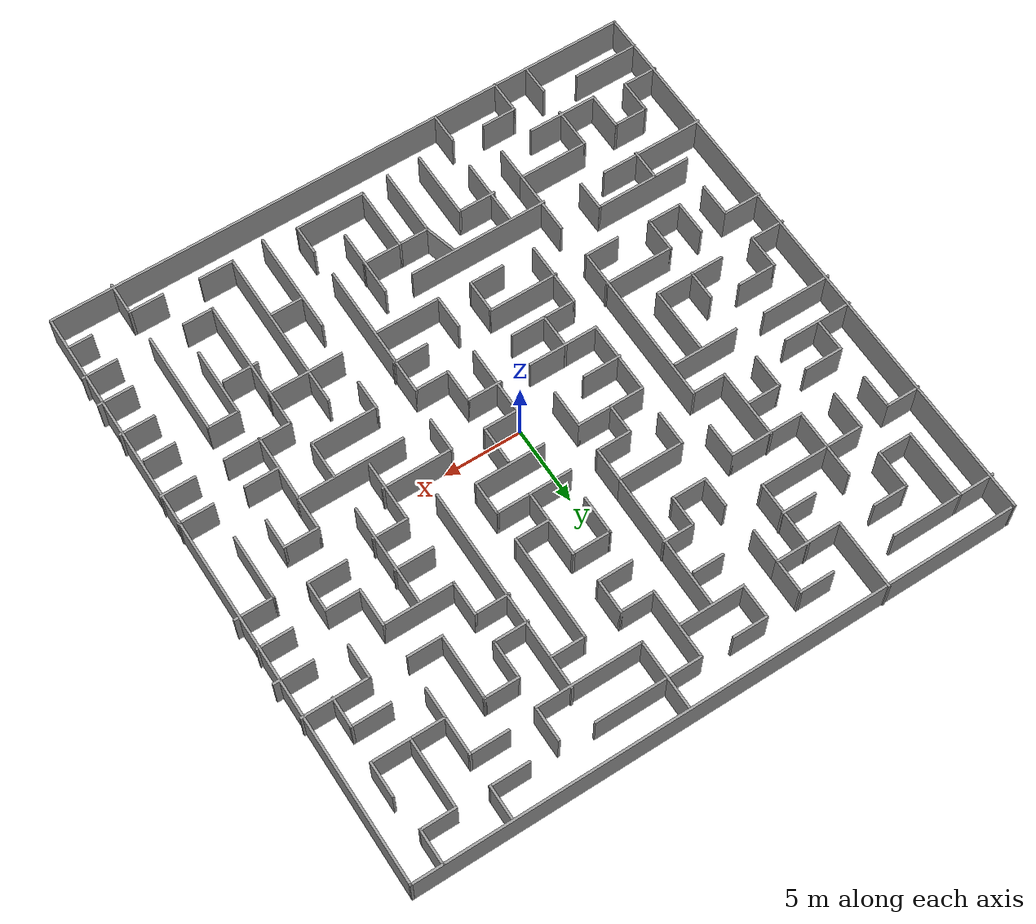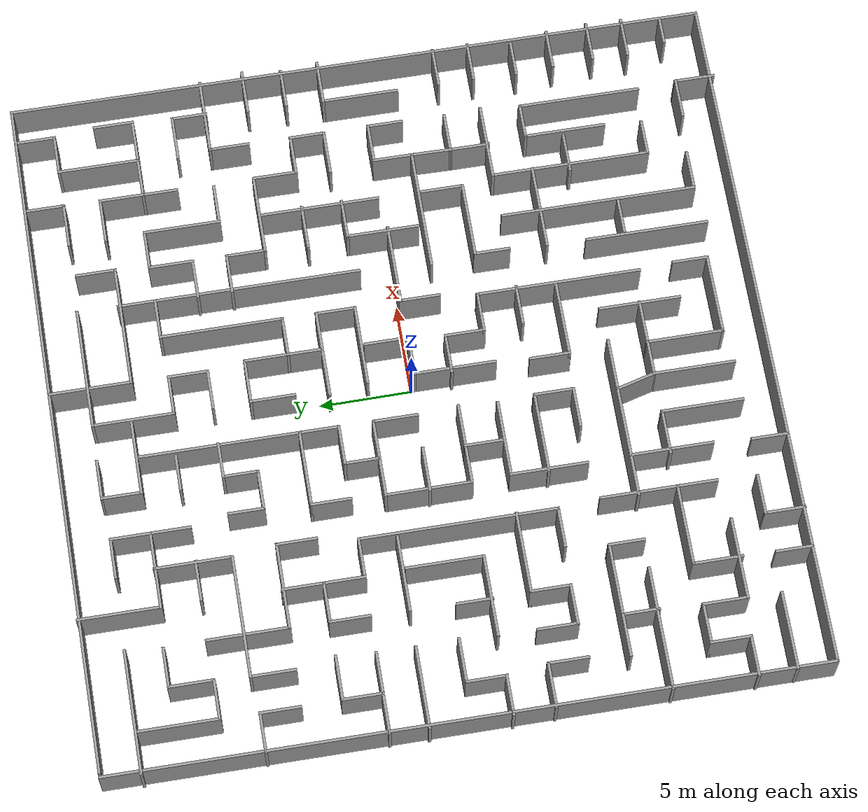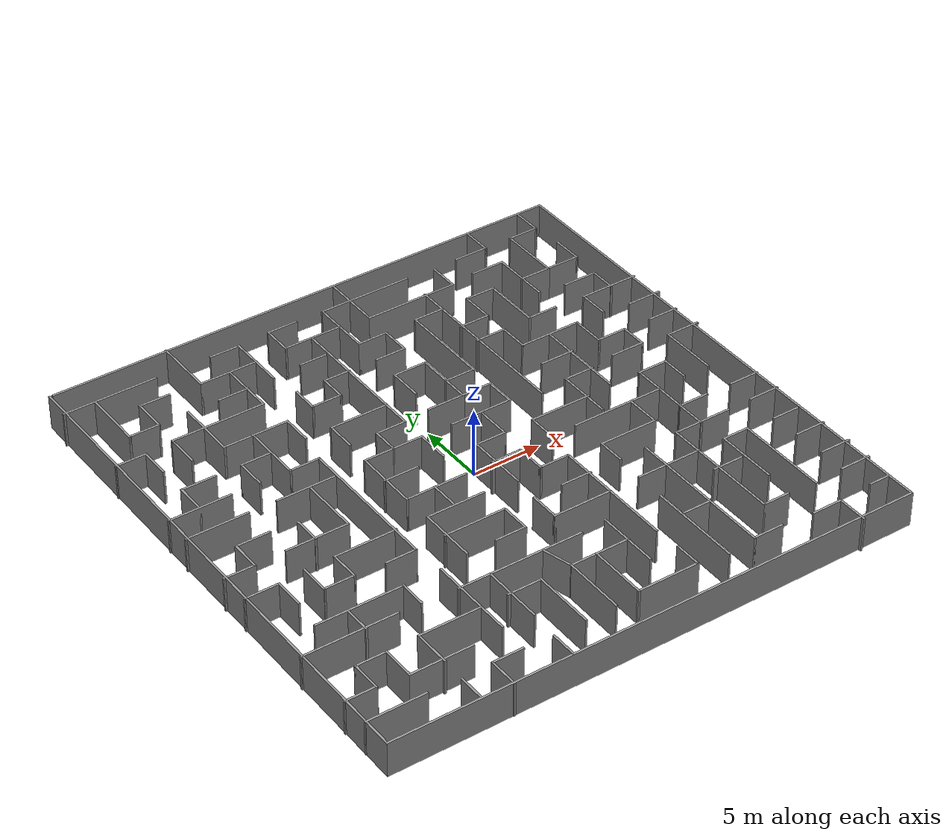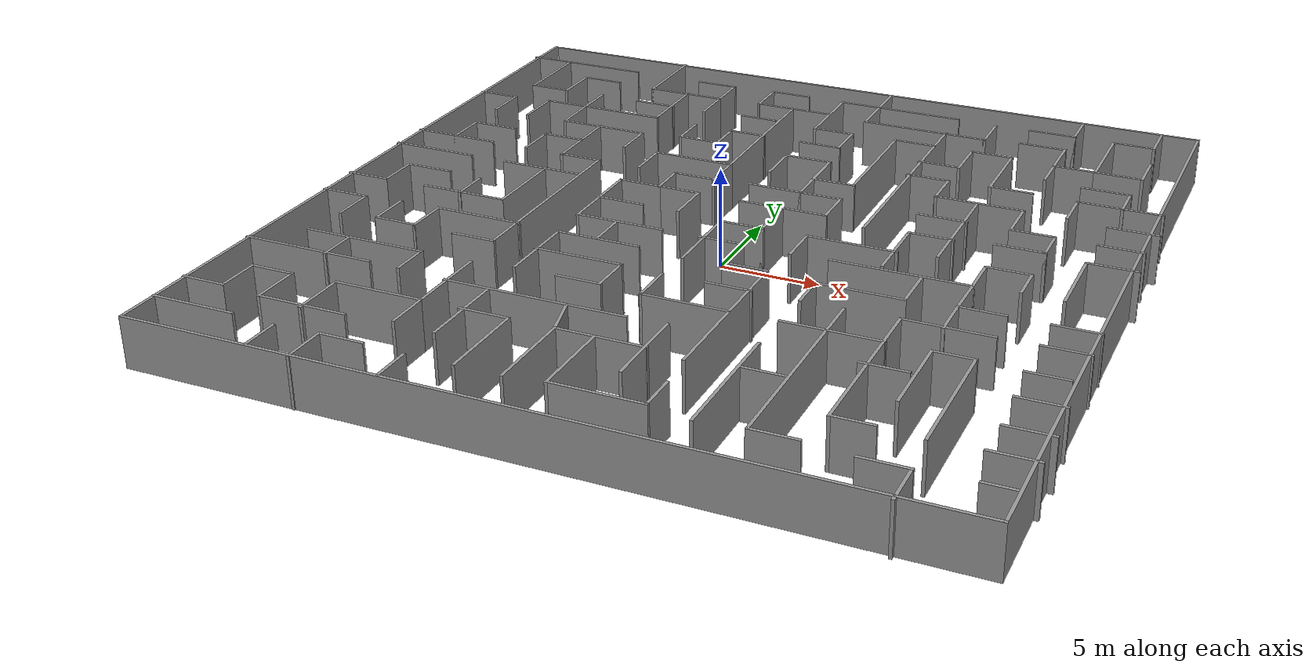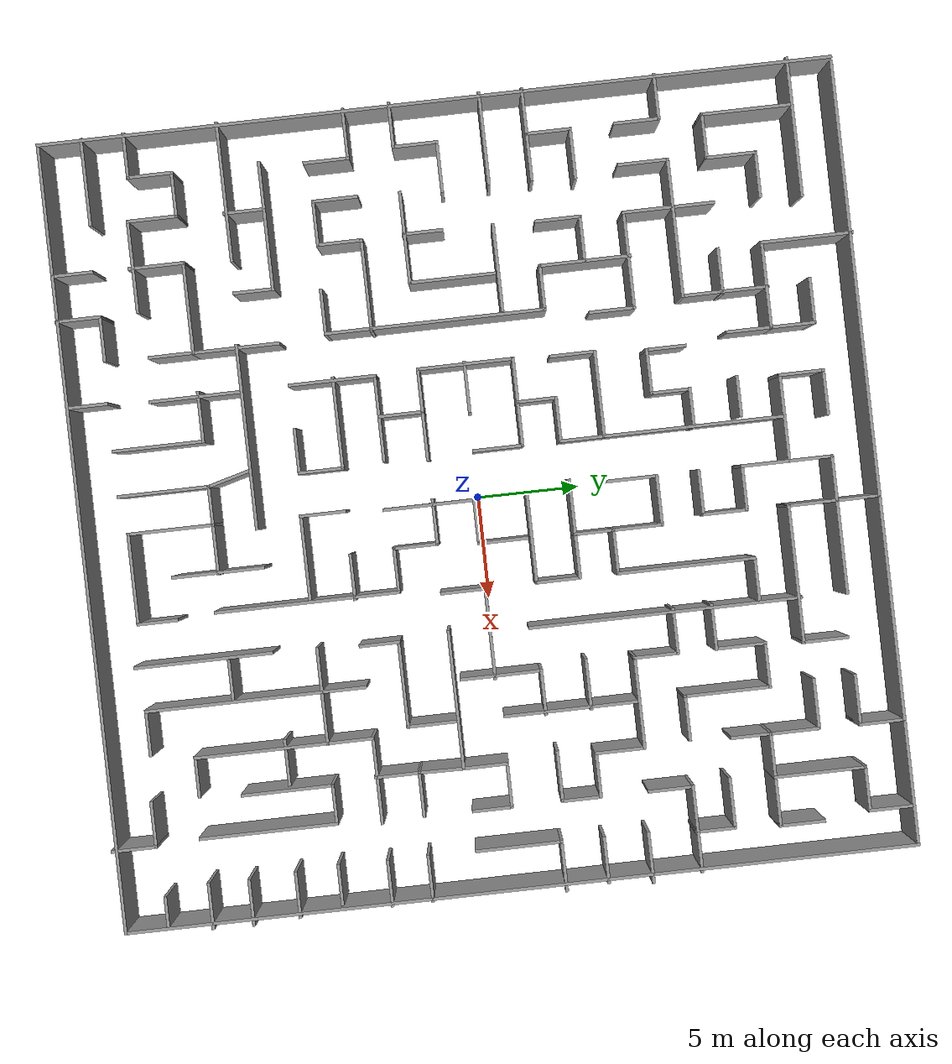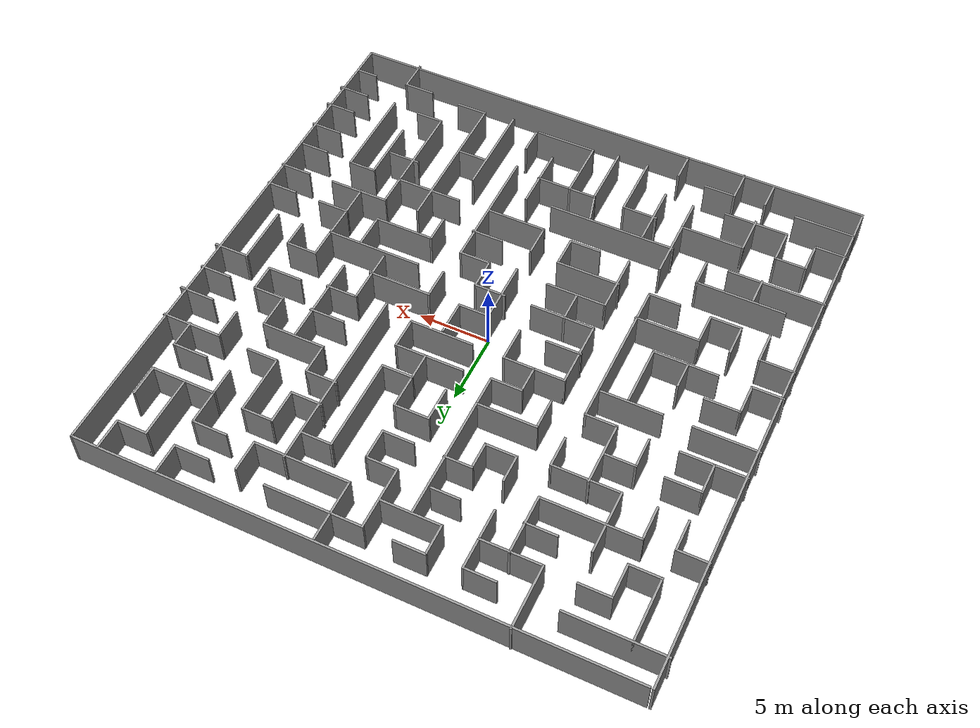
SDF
<?xml version='1.0'?>
<sdf version='1.7'>
  <model name='complex_maze'>
    <pose>-0.002641 -0.038098 0 0 -0 0</pose>
    <link name='Wall_0'>
      <collision name='Wall_0_Collision'>
        <geometry>
          <box>
            <size>38.5 0.15 2.5</size>
          </box>
        </geometry>
        <pose>0 0 1.25 0 -0 0</pose>
      </collision>
      <visual name='Wall_0_Visual'>
        <pose>0 0 1.25 0 -0 0</pose>
        <geometry>
          <box>
            <size>38.5 0.15 2.5</size>
          </box>
        </geometry>
        <material>
          <script>
            <uri>file://media/materials/scripts/gazebo.material</uri>
            <name>Gazebo/Grey</name>
          </script>
          <ambient>1 1 1 1</ambient>
        </material>
        <meta>
          <layer>0</layer>
        </meta>
      </visual>
      <pose>-19.1643 0.058416 0 0 -0 -1.5708</pose>
    </link>
    <link name='Wall_10'>
      <collision name='Wall_10_Collision'>
        <geometry>
          <box>
            <size>2.5 0.15 2.5</size>
          </box>
        </geometry>
        <pose>0 0 1.25 0 -0 0</pose>
      </collision>
      <visual name='Wall_10_Visual'>
        <pose>0 0 1.25 0 -0 0</pose>
        <geometry>
          <box>
            <size>2.5 0.15 2.5</size>
          </box>
        </geometry>
        <material>
          <script>
            <uri>file://media/materials/scripts/gazebo.material</uri>
            <name>Gazebo/Grey</name>
          </script>
          <ambient>1 1 1 1</ambient>
        </material>
        <meta>
          <layer>0</layer>
        </meta>
      </visual>
      <pose>-14.9959 13.9601 0 0 -0 1.5708</pose>
    </link>
    <link name='Wall_100'>
      <collision name='Wall_100_Collision'>
        <geometry>
          <box>
            <size>2.25 0.15 2.5</size>
          </box>
        </geometry>
        <pose>0 0 1.25 0 -0 0</pose>
      </collision>
      <visual name='Wall_100_Visual'>
        <pose>0 0 1.25 0 -0 0</pose>
        <geometry>
          <box>
            <size>2.25 0.15 2.5</size>
          </box>
        </geometry>
        <material>
          <script>
            <uri>file://media/materials/scripts/gazebo.material</uri>
            <name>Gazebo/Grey</name>
          </script>
          <ambient>1 1 1 1</ambient>
        </material>
        <meta>
          <layer>0</layer>
        </meta>
      </visual>
      <pose>17.9525 -4.25699 0 0 -0 3.14159</pose>
    </link>
    <link name='Wall_102'>
      <collision name='Wall_102_Collision'>
        <geometry>
          <box>
            <size>2.25 0.15 2.5</size>
          </box>
        </geometry>
        <pose>0 0 1.25 0 -0 0</pose>
      </collision>
      <visual name='Wall_102_Visual'>
        <pose>0 0 1.25 0 -0 0</pose>
        <geometry>
          <box>
            <size>2.25 0.15 2.5</size>
          </box>
        </geometry>
        <material>
          <script>
            <uri>file://media/materials/scripts/gazebo.material</uri>
            <name>Gazebo/Grey</name>
          </script>
          <ambient>1 1 1 1</ambient>
        </material>
        <meta>
          <layer>0</layer>
        </meta>
      </visual>
      <pose>17.9724 -6.21477 0 0 -0 0</pose>
    </link>
    <link name='Wall_104'>
      <collision name='Wall_104_Collision'>
        <geometry>
          <box>
            <size>2.25 0.15 2.5</size>
          </box>
        </geometry>
        <pose>0 0 1.25 0 -0 0</pose>
      </collision>
      <visual name='Wall_104_Visual'>
        <pose>0 0 1.25 0 -0 0</pose>
        <geometry>
          <box>
            <size>2.25 0.15 2.5</size>
          </box>
        </geometry>
        <material>
          <script>
            <uri>file://media/materials/scripts/gazebo.material</uri>
            <name>Gazebo/Grey</name>
          </script>
          <ambient>1 1 1 1</ambient>
        </material>
        <meta>
          <layer>0</layer>
        </meta>
      </visual>
      <pose>18.0336 -10.6809 0 0 -0 0</pose>
    </link>
    <link name='Wall_106'>
      <collision name='Wall_106_Collision'>
        <geometry>
          <box>
            <size>2.25 0.15 2.5</size>
          </box>
        </geometry>
        <pose>0 0 1.25 0 -0 0</pose>
      </collision>
      <visual name='Wall_106_Visual'>
        <pose>0 0 1.25 0 -0 0</pose>
        <geometry>
          <box>
            <size>2.25 0.15 2.5</size>
          </box>
        </geometry>
        <material>
          <script>
            <uri>file://media/materials/scripts/gazebo.material</uri>
            <name>Gazebo/Grey</name>
          </script>
          <ambient>1 1 1 1</ambient>
        </material>
        <meta>
          <layer>0</layer>
        </meta>
      </visual>
      <pose>18.1559 -12.9446 0 0 -0 0</pose>
    </link>
    <link name='Wall_108'>
      <collision name='Wall_108_Collision'>
        <geometry>
          <box>
            <size>2.25 0.15 2.5</size>
          </box>
        </geometry>
        <pose>0 0 1.25 0 -0 0</pose>
      </collision>
      <visual name='Wall_108_Visual'>
        <pose>0 0 1.25 0 -0 0</pose>
        <geometry>
          <box>
            <size>2.25 0.15 2.5</size>
          </box>
        </geometry>
        <material>
          <script>
            <uri>file://media/materials/scripts/gazebo.material</uri>
            <name>Gazebo/Grey</name>
          </script>
          <ambient>1 1 1 1</ambient>
        </material>
        <meta>
          <layer>0</layer>
        </meta>
      </visual>
      <pose>18.0947 -14.9024 0 0 -0 0</pose>
    </link>
    <link name='Wall_11'>
      <collision name='Wall_11_Collision'>
        <geometry>
          <box>
            <size>2.25 0.15 2.5</size>
          </box>
        </geometry>
        <pose>0 0 1.25 0 -0 0</pose>
      </collision>
      <visual name='Wall_11_Visual'>
        <pose>0 0 1.25 0 -0 0</pose>
        <geometry>
          <box>
            <size>2.25 0.15 2.5</size>
          </box>
        </geometry>
        <material>
          <script>
            <uri>file://media/materials/scripts/gazebo.material</uri>
            <name>Gazebo/Grey</name>
          </script>
          <ambient>1 1 1 1</ambient>
        </material>
        <meta>
          <layer>0</layer>
        </meta>
      </visual>
      <pose>-13.9459 15.1351 0 0 -0 0</pose>
    </link>
    <link name='Wall_110'>
      <collision name='Wall_110_Collision'>
        <geometry>
          <box>
            <size>1.5 0.15 2.5</size>
          </box>
        </geometry>
        <pose>0 0 1.25 0 -0 0</pose>
      </collision>
      <visual name='Wall_110_Visual'>
        <pose>0 0 1.25 0 -0 0</pose>
        <geometry>
          <box>
            <size>1.5 0.15 2.5</size>
          </box>
        </geometry>
        <material>
          <script>
            <uri>file://media/materials/scripts/gazebo.material</uri>
            <name>Gazebo/Grey</name>
          </script>
          <ambient>1 1 1 1</ambient>
        </material>
        <meta>
          <layer>0</layer>
        </meta>
      </visual>
      <pose>18.148 -17.0437 0 0 -0 0</pose>
    </link>
    <link name='Wall_112'>
      <collision name='Wall_112_Collision'>
        <geometry>
          <box>
            <size>2 0.15 2.5</size>
          </box>
        </geometry>
        <pose>0 0 1.25 0 -0 0</pose>
      </collision>
      <visual name='Wall_112_Visual'>
        <pose>0 0 1.25 0 -0 0</pose>
        <geometry>
          <box>
            <size>2 0.15 2.5</size>
          </box>
        </geometry>
        <material>
          <script>
            <uri>file://media/materials/scripts/gazebo.material</uri>
            <name>Gazebo/Grey</name>
          </script>
          <ambient>1 1 1 1</ambient>
        </material>
        <meta>
          <layer>0</layer>
        </meta>
      </visual>
      <pose>17.7862 -8.60081 0 0 -0 0</pose>
    </link>
    <link name='Wall_114'>
      <collision name='Wall_114_Collision'>
        <geometry>
          <box>
            <size>2.25 0.15 2.5</size>
          </box>
        </geometry>
        <pose>0 0 1.25 0 -0 0</pose>
      </collision>
      <visual name='Wall_114_Visual'>
        <pose>0 0 1.25 0 -0 0</pose>
        <geometry>
          <box>
            <size>2.25 0.15 2.5</size>
          </box>
        </geometry>
        <material>
          <script>
            <uri>file://media/materials/scripts/gazebo.material</uri>
            <name>Gazebo/Grey</name>
          </script>
          <ambient>1 1 1 1</ambient>
        </material>
        <meta>
          <layer>0</layer>
        </meta>
      </visual>
      <pose>14.9646 -18.2574 0 0 -0 1.5708</pose>
    </link>
    <link name='Wall_115'>
      <collision name='Wall_115_Collision'>
        <geometry>
          <box>
            <size>2.25 0.15 2.5</size>
          </box>
        </geometry>
        <pose>0 0 1.25 0 -0 0</pose>
      </collision>
      <visual name='Wall_115_Visual'>
        <pose>0 0 1.25 0 -0 0</pose>
        <geometry>
          <box>
            <size>2.25 0.15 2.5</size>
          </box>
        </geometry>
        <material>
          <script>
            <uri>file://media/materials/scripts/gazebo.material</uri>
            <name>Gazebo/Grey</name>
          </script>
          <ambient>1 1 1 1</ambient>
        </material>
        <meta>
          <layer>0</layer>
        </meta>
      </visual>
      <pose>13.9146 -17.2074 0 0 -0 3.14159</pose>
    </link>
    <link name='Wall_117'>
      <collision name='Wall_117_Collision'>
        <geometry>
          <box>
            <size>2 0.15 2.5</size>
          </box>
        </geometry>
        <pose>0 0 1.25 0 -0 0</pose>
      </collision>
      <visual name='Wall_117_Visual'>
        <pose>0 0 1.25 0 -0 0</pose>
        <geometry>
          <box>
            <size>2 0.15 2.5</size>
          </box>
        </geometry>
        <material>
          <script>
            <uri>file://media/materials/scripts/gazebo.material</uri>
            <name>Gazebo/Grey</name>
          </script>
          <ambient>1 1 1 1</ambient>
        </material>
        <meta>
          <layer>0</layer>
        </meta>
      </visual>
      <pose>-6.45183 -18.144 0 0 -0 1.5708</pose>
    </link>
    <link name='Wall_119'>
      <collision name='Wall_119_Collision'>
        <geometry>
          <box>
            <size>2.25 0.15 2.5</size>
          </box>
        </geometry>
        <pose>0 0 1.25 0 -0 0</pose>
      </collision>
      <visual name='Wall_119_Visual'>
        <pose>0 0 1.25 0 -0 0</pose>
        <geometry>
          <box>
            <size>2.25 0.15 2.5</size>
          </box>
        </geometry>
        <material>
          <script>
            <uri>file://media/materials/scripts/gazebo.material</uri>
            <name>Gazebo/Grey</name>
          </script>
          <ambient>1 1 1 1</ambient>
        </material>
        <meta>
          <layer>0</layer>
        </meta>
      </visual>
      <pose>-10.639 -18.112 0 0 -0 1.5708</pose>
    </link>
    <link name='Wall_120'>
      <collision name='Wall_120_Collision'>
        <geometry>
          <box>
            <size>2.25 0.15 2.5</size>
          </box>
        </geometry>
        <pose>0 0 1.25 0 -0 0</pose>
      </collision>
      <visual name='Wall_120_Visual'>
        <pose>0 0 1.25 0 -0 0</pose>
        <geometry>
          <box>
            <size>2.25 0.15 2.5</size>
          </box>
        </geometry>
        <material>
          <script>
            <uri>file://media/materials/scripts/gazebo.material</uri>
            <name>Gazebo/Grey</name>
          </script>
          <ambient>1 1 1 1</ambient>
        </material>
        <meta>
          <layer>0</layer>
        </meta>
      </visual>
      <pose>-9.58898 -17.062 0 0 -0 0</pose>
    </link>
    <link name='Wall_122'>
      <collision name='Wall_122_Collision'>
        <geometry>
          <box>
            <size>2 0.15 2.5</size>
          </box>
        </geometry>
        <pose>0 0 1.25 0 -0 0</pose>
      </collision>
      <visual name='Wall_122_Visual'>
        <pose>0 0 1.25 0 -0 0</pose>
        <geometry>
          <box>
            <size>2 0.15 2.5</size>
          </box>
        </geometry>
        <material>
          <script>
            <uri>file://media/materials/scripts/gazebo.material</uri>
            <name>Gazebo/Grey</name>
          </script>
          <ambient>1 1 1 1</ambient>
        </material>
        <meta>
          <layer>0</layer>
        </meta>
      </visual>
      <pose>-12.8256 -18.144 0 0 -0 1.5708</pose>
    </link>
    <link name='Wall_124'>
      <collision name='Wall_124_Collision'>
        <geometry>
          <box>
            <size>4.25 0.15 2.5</size>
          </box>
        </geometry>
        <pose>0 0 1.25 0 -0 0</pose>
      </collision>
      <visual name='Wall_124_Visual'>
        <pose>0 0 1.25 0 -0 0</pose>
        <geometry>
          <box>
            <size>4.25 0.15 2.5</size>
          </box>
        </geometry>
        <material>
          <script>
            <uri>file://media/materials/scripts/gazebo.material</uri>
            <name>Gazebo/Grey</name>
          </script>
          <ambient>1 1 1 1</ambient>
        </material>
        <meta>
          <layer>0</layer>
        </meta>
      </visual>
      <pose>-17.1494 -17.0219 0 0 -0 0</pose>
    </link>
    <link name='Wall_126'>
      <collision name='Wall_126_Collision'>
        <geometry>
          <box>
            <size>2.25 0.15 2.5</size>
          </box>
        </geometry>
        <pose>0 0 1.25 0 -0 0</pose>
      </collision>
      <visual name='Wall_126_Visual'>
        <pose>0 0 1.25 0 -0 0</pose>
        <geometry>
          <box>
            <size>2.25 0.15 2.5</size>
          </box>
        </geometry>
        <material>
          <script>
            <uri>file://media/materials/scripts/gazebo.material</uri>
            <name>Gazebo/Grey</name>
          </script>
          <ambient>1 1 1 1</ambient>
        </material>
        <meta>
          <layer>0</layer>
        </meta>
      </visual>
      <pose>-18.1959 -14.9749 0 0 -0 0</pose>
    </link>
    <link name='Wall_127'>
      <collision name='Wall_127_Collision'>
        <geometry>
          <box>
            <size>2.25 0.15 2.5</size>
          </box>
        </geometry>
        <pose>0 0 1.25 0 -0 0</pose>
      </collision>
      <visual name='Wall_127_Visual'>
        <pose>0 0 1.25 0 -0 0</pose>
        <geometry>
          <box>
            <size>2.25 0.15 2.5</size>
          </box>
        </geometry>
        <material>
          <script>
            <uri>file://media/materials/scripts/gazebo.material</uri>
            <name>Gazebo/Grey</name>
          </script>
          <ambient>1 1 1 1</ambient>
        </material>
        <meta>
          <layer>0</layer>
        </meta>
      </visual>
      <pose>-17.1459 -13.9249 0 0 -0 1.5708</pose>
    </link>
    <link name='Wall_128'>
      <collision name='Wall_128_Collision'>
        <geometry>
          <box>
            <size>2.25 0.15 2.5</size>
          </box>
        </geometry>
        <pose>0 0 1.25 0 -0 0</pose>
      </collision>
      <visual name='Wall_128_Visual'>
        <pose>0 0 1.25 0 -0 0</pose>
        <geometry>
          <box>
            <size>2.25 0.15 2.5</size>
          </box>
        </geometry>
        <material>
          <script>
            <uri>file://media/materials/scripts/gazebo.material</uri>
            <name>Gazebo/Grey</name>
          </script>
          <ambient>1 1 1 1</ambient>
        </material>
        <meta>
          <layer>0</layer>
        </meta>
      </visual>
      <pose>-16.0959 -12.8749 0 0 -0 0</pose>
    </link>
    <link name='Wall_129'>
      <collision name='Wall_129_Collision'>
        <geometry>
          <box>
            <size>2.5 0.15 2.5</size>
          </box>
        </geometry>
        <pose>0 0 1.25 0 -0 0</pose>
      </collision>
      <visual name='Wall_129_Visual'>
        <pose>0 0 1.25 0 -0 0</pose>
        <geometry>
          <box>
            <size>2.5 0.15 2.5</size>
          </box>
        </geometry>
        <material>
          <script>
            <uri>file://media/materials/scripts/gazebo.material</uri>
            <name>Gazebo/Grey</name>
          </script>
          <ambient>1 1 1 1</ambient>
        </material>
        <meta>
          <layer>0</layer>
        </meta>
      </visual>
      <pose>-15.0459 -14.0499 0 0 -0 -1.5708</pose>
    </link>
    <link name='Wall_13'>
      <collision name='Wall_13_Collision'>
        <geometry>
          <box>
            <size>2.25 0.15 2.5</size>
          </box>
        </geometry>
        <pose>0 0 1.25 0 -0 0</pose>
      </collision>
      <visual name='Wall_13_Visual'>
        <pose>0 0 1.25 0 -0 0</pose>
        <geometry>
          <box>
            <size>2.25 0.15 2.5</size>
          </box>
        </geometry>
        <material>
          <script>
            <uri>file://media/materials/scripts/gazebo.material</uri>
            <name>Gazebo/Grey</name>
          </script>
          <ambient>1 1 1 1</ambient>
        </material>
        <meta>
          <layer>0</layer>
        </meta>
      </visual>
      <pose>-18.178 10.6988 0 0 -0 0</pose>
    </link>
    <link name='Wall_130'>
      <collision name='Wall_130_Collision'>
        <geometry>
          <box>
            <size>4.5 0.15 2.5</size>
          </box>
        </geometry>
        <pose>0 0 1.25 0 -0 0</pose>
      </collision>
      <visual name='Wall_130_Visual'>
        <pose>0 0 1.25 0 -0 0</pose>
        <geometry>
          <box>
            <size>4.5 0.15 2.5</size>
          </box>
        </geometry>
        <material>
          <script>
            <uri>file://media/materials/scripts/gazebo.material</uri>
            <name>Gazebo/Grey</name>
          </script>
          <ambient>1 1 1 1</ambient>
        </material>
        <meta>
          <layer>0</layer>
        </meta>
      </visual>
      <pose>-12.8709 -15.2249 0 0 -0 0</pose>
    </link>
    <link name='Wall_132'>
      <collision name='Wall_132_Collision'>
        <geometry>
          <box>
            <size>2.75 0.15 2.5</size>
          </box>
        </geometry>
        <pose>0 0 1.25 0 -0 0</pose>
      </collision>
      <visual name='Wall_132_Visual'>
        <pose>0 0 1.25 0 -0 0</pose>
        <geometry>
          <box>
            <size>2.75 0.15 2.5</size>
          </box>
        </geometry>
        <material>
          <script>
            <uri>file://media/materials/scripts/gazebo.material</uri>
            <name>Gazebo/Grey</name>
          </script>
          <ambient>1 1 1 1</ambient>
        </material>
        <meta>
          <layer>0</layer>
        </meta>
      </visual>
      <pose>-12.7791 -14.0936 0 0 -0 1.5708</pose>
    </link>
    <link name='Wall_133'>
      <collision name='Wall_133_Collision'>
        <geometry>
          <box>
            <size>4.5 0.15 2.5</size>
          </box>
        </geometry>
        <pose>0 0 1.25 0 -0 0</pose>
      </collision>
      <visual name='Wall_133_Visual'>
        <pose>0 0 1.25 0 -0 0</pose>
        <geometry>
          <box>
            <size>4.5 0.15 2.5</size>
          </box>
        </geometry>
        <material>
          <script>
            <uri>file://media/materials/scripts/gazebo.material</uri>
            <name>Gazebo/Grey</name>
          </script>
          <ambient>1 1 1 1</ambient>
        </material>
        <meta>
          <layer>0</layer>
        </meta>
      </visual>
      <pose>-10.6041 -12.7936 0 0 -0 0</pose>
    </link>
    <link name='Wall_134'>
      <collision name='Wall_134_Collision'>
        <geometry>
          <box>
            <size>4.25 0.15 2.5</size>
          </box>
        </geometry>
        <pose>0 0 1.25 0 -0 0</pose>
      </collision>
      <visual name='Wall_134_Visual'>
        <pose>0 0 1.25 0 -0 0</pose>
        <geometry>
          <box>
            <size>4.25 0.15 2.5</size>
          </box>
        </geometry>
        <material>
          <script>
            <uri>file://media/materials/scripts/gazebo.material</uri>
            <name>Gazebo/Grey</name>
          </script>
          <ambient>1 1 1 1</ambient>
        </material>
        <meta>
          <layer>0</layer>
        </meta>
      </visual>
      <pose>-8.42908 -10.7436 0 0 -0 1.5708</pose>
    </link>
    <link name='Wall_136'>
      <collision name='Wall_136_Collision'>
        <geometry>
          <box>
            <size>2.25 0.15 2.5</size>
          </box>
        </geometry>
        <pose>0 0 1.25 0 -0 0</pose>
      </collision>
      <visual name='Wall_136_Visual'>
        <pose>0 0 1.25 0 -0 0</pose>
        <geometry>
          <box>
            <size>2.25 0.15 2.5</size>
          </box>
        </geometry>
        <material>
          <script>
            <uri>file://media/materials/scripts/gazebo.material</uri>
            <name>Gazebo/Grey</name>
          </script>
          <ambient>1 1 1 1</ambient>
        </material>
        <meta>
          <layer>0</layer>
        </meta>
      </visual>
      <pose>-8.42908 -13.8436 0 0 -0 -1.5708</pose>
    </link>
    <link name='Wall_138'>
      <collision name='Wall_138_Collision'>
        <geometry>
          <box>
            <size>9 0.15 2.5</size>
          </box>
        </geometry>
        <pose>0 0 1.25 0 -0 0</pose>
      </collision>
      <visual name='Wall_138_Visual'>
        <pose>0 0 1.25 0 -0 0</pose>
        <geometry>
          <box>
            <size>9 0.15 2.5</size>
          </box>
        </geometry>
        <material>
          <script>
            <uri>file://media/materials/scripts/gazebo.material</uri>
            <name>Gazebo/Grey</name>
          </script>
          <ambient>1 1 1 1</ambient>
        </material>
        <meta>
          <layer>0</layer>
        </meta>
      </visual>
      <pose>-4.1204 -10.6947 0 0 -0 0</pose>
    </link>
    <link name='Wall_14'>
      <collision name='Wall_14_Collision'>
        <geometry>
          <box>
            <size>2.25 0.15 2.5</size>
          </box>
        </geometry>
        <pose>0 0 1.25 0 -0 0</pose>
      </collision>
      <visual name='Wall_14_Visual'>
        <pose>0 0 1.25 0 -0 0</pose>
        <geometry>
          <box>
            <size>2.25 0.15 2.5</size>
          </box>
        </geometry>
        <material>
          <script>
            <uri>file://media/materials/scripts/gazebo.material</uri>
            <name>Gazebo/Grey</name>
          </script>
          <ambient>1 1 1 1</ambient>
        </material>
        <meta>
          <layer>0</layer>
        </meta>
      </visual>
      <pose>-17.128 9.64878 0 0 -0 -1.5708</pose>
    </link>
    <link name='Wall_140'>
      <collision name='Wall_140_Collision'>
        <geometry>
          <box>
            <size>2 0.15 2.5</size>
          </box>
        </geometry>
        <pose>0 0 1.25 0 -0 0</pose>
      </collision>
      <visual name='Wall_140_Visual'>
        <pose>0 0 1.25 0 -0 0</pose>
        <geometry>
          <box>
            <size>2 0.15 2.5</size>
          </box>
        </geometry>
        <material>
          <script>
            <uri>file://media/materials/scripts/gazebo.material</uri>
            <name>Gazebo/Grey</name>
          </script>
          <ambient>1 1 1 1</ambient>
        </material>
        <meta>
          <layer>0</layer>
        </meta>
      </visual>
      <pose>4.24868 -15.9464 0 0 -0 -1.5708</pose>
    </link>
    <link name='Wall_141'>
      <collision name='Wall_141_Collision'>
        <geometry>
          <box>
            <size>4.5 0.15 2.5</size>
          </box>
        </geometry>
        <pose>0 0 1.25 0 -0 0</pose>
      </collision>
      <visual name='Wall_141_Visual'>
        <pose>0 0 1.25 0 -0 0</pose>
        <geometry>
          <box>
            <size>4.5 0.15 2.5</size>
          </box>
        </geometry>
        <material>
          <script>
            <uri>file://media/materials/scripts/gazebo.material</uri>
            <name>Gazebo/Grey</name>
          </script>
          <ambient>1 1 1 1</ambient>
        </material>
        <meta>
          <layer>0</layer>
        </meta>
      </visual>
      <pose>2.07368 -16.8714 0 0 -0 3.14159</pose>
    </link>
    <link name='Wall_142'>
      <collision name='Wall_142_Collision'>
        <geometry>
          <box>
            <size>4.25 0.15 2.5</size>
          </box>
        </geometry>
        <pose>0 0 1.25 0 -0 0</pose>
      </collision>
      <visual name='Wall_142_Visual'>
        <pose>0 0 1.25 0 -0 0</pose>
        <geometry>
          <box>
            <size>4.25 0.15 2.5</size>
          </box>
        </geometry>
        <material>
          <script>
            <uri>file://media/materials/scripts/gazebo.material</uri>
            <name>Gazebo/Grey</name>
          </script>
          <ambient>1 1 1 1</ambient>
        </material>
        <meta>
          <layer>0</layer>
        </meta>
      </visual>
      <pose>-0.101325 -14.8214 0 0 -0 1.5708</pose>
    </link>
    <link name='Wall_143'>
      <collision name='Wall_143_Collision'>
        <geometry>
          <box>
            <size>2 0.15 2.5</size>
          </box>
        </geometry>
        <pose>0 0 1.25 0 -0 0</pose>
      </collision>
      <visual name='Wall_143_Visual'>
        <pose>0 0 1.25 0 -0 0</pose>
        <geometry>
          <box>
            <size>2 0.15 2.5</size>
          </box>
        </geometry>
        <material>
          <script>
            <uri>file://media/materials/scripts/gazebo.material</uri>
            <name>Gazebo/Grey</name>
          </script>
          <ambient>1 1 1 1</ambient>
        </material>
        <meta>
          <layer>0</layer>
        </meta>
      </visual>
      <pose>-1.02632 -12.7714 0 0 -0 3.14159</pose>
    </link>
    <link name='Wall_144'>
      <collision name='Wall_144_Collision'>
        <geometry>
          <box>
            <size>2.25 0.15 2.5</size>
          </box>
        </geometry>
        <pose>0 0 1.25 0 -0 0</pose>
      </collision>
      <visual name='Wall_144_Visual'>
        <pose>0 0 1.25 0 -0 0</pose>
        <geometry>
          <box>
            <size>2.25 0.15 2.5</size>
          </box>
        </geometry>
        <material>
          <script>
            <uri>file://media/materials/scripts/gazebo.material</uri>
            <name>Gazebo/Grey</name>
          </script>
          <ambient>1 1 1 1</ambient>
        </material>
        <meta>
          <layer>0</layer>
        </meta>
      </visual>
      <pose>-2.22309 -11.7572 0 0 -0 1.8326</pose>
    </link>
    <link name='Wall_146'>
      <collision name='Wall_146_Collision'>
        <geometry>
          <box>
            <size>4.5 0.15 2.5</size>
          </box>
        </geometry>
        <pose>0 0 1.25 0 -0 0</pose>
      </collision>
      <visual name='Wall_146_Visual'>
        <pose>0 0 1.25 0 -0 0</pose>
        <geometry>
          <box>
            <size>4.5 0.15 2.5</size>
          </box>
        </geometry>
        <material>
          <script>
            <uri>file://media/materials/scripts/gazebo.material</uri>
            <name>Gazebo/Grey</name>
          </script>
          <ambient>1 1 1 1</ambient>
        </material>
        <meta>
          <layer>0</layer>
        </meta>
      </visual>
      <pose>-1.95132 -14.9464 0 0 -0 -1.5708</pose>
    </link>
    <link name='Wall_148'>
      <collision name='Wall_148_Collision'>
        <geometry>
          <box>
            <size>4.5 0.15 2.5</size>
          </box>
        </geometry>
        <pose>0 0 1.25 0 -0 0</pose>
      </collision>
      <visual name='Wall_148_Visual'>
        <pose>0 0 1.25 0 -0 0</pose>
        <geometry>
          <box>
            <size>4.5 0.15 2.5</size>
          </box>
        </geometry>
        <material>
          <script>
            <uri>file://media/materials/scripts/gazebo.material</uri>
            <name>Gazebo/Grey</name>
          </script>
          <ambient>1 1 1 1</ambient>
        </material>
        <meta>
          <layer>0</layer>
        </meta>
      </visual>
      <pose>2.20162 -12.7766 0 0 -0 -1.5708</pose>
    </link>
    <link name='Wall_150'>
      <collision name='Wall_150_Collision'>
        <geometry>
          <box>
            <size>2.5 0.15 2.5</size>
          </box>
        </geometry>
        <pose>0 0 1.25 0 -0 0</pose>
      </collision>
      <visual name='Wall_150_Visual'>
        <pose>0 0 1.25 0 -0 0</pose>
        <geometry>
          <box>
            <size>2.5 0.15 2.5</size>
          </box>
        </geometry>
        <material>
          <script>
            <uri>file://media/materials/scripts/gazebo.material</uri>
            <name>Gazebo/Grey</name>
          </script>
          <ambient>1 1 1 1</ambient>
        </material>
        <meta>
          <layer>0</layer>
        </meta>
      </visual>
      <pose>1.07367 -12.7714 0 0 -0 0</pose>
    </link>
    <link name='Wall_152'>
      <collision name='Wall_152_Collision'>
        <geometry>
          <box>
            <size>4.5 0.15 2.5</size>
          </box>
        </geometry>
        <pose>0 0 1.25 0 -0 0</pose>
      </collision>
      <visual name='Wall_152_Visual'>
        <pose>0 0 1.25 0 -0 0</pose>
        <geometry>
          <box>
            <size>4.5 0.15 2.5</size>
          </box>
        </geometry>
        <material>
          <script>
            <uri>file://media/materials/scripts/gazebo.material</uri>
            <name>Gazebo/Grey</name>
          </script>
          <ambient>1 1 1 1</ambient>
        </material>
        <meta>
          <layer>0</layer>
        </meta>
      </visual>
      <pose>-6.31225 -12.9162 0 0 -0 -1.5708</pose>
    </link>
    <link name='Wall_154'>
      <collision name='Wall_154_Collision'>
        <geometry>
          <box>
            <size>2.5 0.15 2.5</size>
          </box>
        </geometry>
        <pose>0 0 1.25 0 -0 0</pose>
      </collision>
      <visual name='Wall_154_Visual'>
        <pose>0 0 1.25 0 -0 0</pose>
        <geometry>
          <box>
            <size>2.5 0.15 2.5</size>
          </box>
        </geometry>
        <material>
          <script>
            <uri>file://media/materials/scripts/gazebo.material</uri>
            <name>Gazebo/Grey</name>
          </script>
          <ambient>1 1 1 1</ambient>
        </material>
        <meta>
          <layer>0</layer>
        </meta>
      </visual>
      <pose>-5.32335 -12.7882 0 0 -0 0</pose>
    </link>
    <link name='Wall_155'>
      <collision name='Wall_155_Collision'>
        <geometry>
          <box>
            <size>4.5 0.15 2.5</size>
          </box>
        </geometry>
        <pose>0 0 1.25 0 -0 0</pose>
      </collision>
      <visual name='Wall_155_Visual'>
        <pose>0 0 1.25 0 -0 0</pose>
        <geometry>
          <box>
            <size>4.5 0.15 2.5</size>
          </box>
        </geometry>
        <material>
          <script>
            <uri>file://media/materials/scripts/gazebo.material</uri>
            <name>Gazebo/Grey</name>
          </script>
          <ambient>1 1 1 1</ambient>
        </material>
        <meta>
          <layer>0</layer>
        </meta>
      </visual>
      <pose>-4.14835 -14.9632 0 0 -0 -1.5708</pose>
    </link>
    <link name='Wall_157'>
      <collision name='Wall_157_Collision'>
        <geometry>
          <box>
            <size>6.75 0.15 2.5</size>
          </box>
        </geometry>
        <pose>0 0 1.25 0 -0 0</pose>
      </collision>
      <visual name='Wall_157_Visual'>
        <pose>0 0 1.25 0 -0 0</pose>
        <geometry>
          <box>
            <size>6.75 0.15 2.5</size>
          </box>
        </geometry>
        <material>
          <script>
            <uri>file://media/materials/scripts/gazebo.material</uri>
            <name>Gazebo/Grey</name>
          </script>
          <ambient>1 1 1 1</ambient>
        </material>
        <meta>
          <layer>0</layer>
        </meta>
      </visual>
      <pose>-15.9459 -10.462 0 0 -0 0</pose>
    </link>
    <link name='Wall_159'>
      <collision name='Wall_159_Collision'>
        <geometry>
          <box>
            <size>2 0.15 2.5</size>
          </box>
        </geometry>
        <pose>0 0 1.25 0 -0 0</pose>
      </collision>
      <visual name='Wall_159_Visual'>
        <pose>0 0 1.25 0 -0 0</pose>
        <geometry>
          <box>
            <size>2 0.15 2.5</size>
          </box>
        </geometry>
        <material>
          <script>
            <uri>file://media/materials/scripts/gazebo.material</uri>
            <name>Gazebo/Grey</name>
          </script>
          <ambient>1 1 1 1</ambient>
        </material>
        <meta>
          <layer>0</layer>
        </meta>
      </visual>
      <pose>-14.9192 -9.6301 0 0 -0 1.5708</pose>
    </link>
    <link name='Wall_16'>
      <collision name='Wall_16_Collision'>
        <geometry>
          <box>
            <size>4.5 0.15 2.5</size>
          </box>
        </geometry>
        <pose>0 0 1.25 0 -0 0</pose>
      </collision>
      <visual name='Wall_16_Visual'>
        <pose>0 0 1.25 0 -0 0</pose>
        <geometry>
          <box>
            <size>4.5 0.15 2.5</size>
          </box>
        </geometry>
        <material>
          <script>
            <uri>file://media/materials/scripts/gazebo.material</uri>
            <name>Gazebo/Grey</name>
          </script>
          <ambient>1 1 1 1</ambient>
        </material>
        <meta>
          <layer>0</layer>
        </meta>
      </visual>
      <pose>-10.6596 17.1324 0 0 -0 -1.5708</pose>
    </link>
    <link name='Wall_161'>
      <collision name='Wall_161_Collision'>
        <geometry>
          <box>
            <size>6.25 0.15 2.5</size>
          </box>
        </geometry>
        <pose>0 0 1.25 0 -0 0</pose>
      </collision>
      <visual name='Wall_161_Visual'>
        <pose>0 0 1.25 0 -0 0</pose>
        <geometry>
          <box>
            <size>6.25 0.15 2.5</size>
          </box>
        </geometry>
        <material>
          <script>
            <uri>file://media/materials/scripts/gazebo.material</uri>
            <name>Gazebo/Grey</name>
          </script>
          <ambient>1 1 1 1</ambient>
        </material>
        <meta>
          <layer>0</layer>
        </meta>
      </visual>
      <pose>-14.1023 -8.64762 0 0 -0 0</pose>
    </link>
    <link name='Wall_162'>
      <collision name='Wall_162_Collision'>
        <geometry>
          <box>
            <size>2 0.15 2.5</size>
          </box>
        </geometry>
        <pose>0 0 1.25 0 -0 0</pose>
      </collision>
      <visual name='Wall_162_Visual'>
        <pose>0 0 1.25 0 -0 0</pose>
        <geometry>
          <box>
            <size>2 0.15 2.5</size>
          </box>
        </geometry>
        <material>
          <script>
            <uri>file://media/materials/scripts/gazebo.material</uri>
            <name>Gazebo/Grey</name>
          </script>
          <ambient>1 1 1 1</ambient>
        </material>
        <meta>
          <layer>0</layer>
        </meta>
      </visual>
      <pose>-11.0523 -9.57262 0 0 -0 -1.5708</pose>
    </link>
    <link name='Wall_164'>
      <collision name='Wall_164_Collision'>
        <geometry>
          <box>
            <size>2.5 0.15 2.5</size>
          </box>
        </geometry>
        <pose>0 0 1.25 0 -0 0</pose>
      </collision>
      <visual name='Wall_164_Visual'>
        <pose>0 0 1.25 0 -0 0</pose>
        <geometry>
          <box>
            <size>2.5 0.15 2.5</size>
          </box>
        </geometry>
        <material>
          <script>
            <uri>file://media/materials/scripts/gazebo.material</uri>
            <name>Gazebo/Grey</name>
          </script>
          <ambient>1 1 1 1</ambient>
        </material>
        <meta>
          <layer>0</layer>
        </meta>
      </visual>
      <pose>-18.0709 -4.36742 0 0 -0 0</pose>
    </link>
    <link name='Wall_165'>
      <collision name='Wall_165_Collision'>
        <geometry>
          <box>
            <size>2.25 0.15 2.5</size>
          </box>
        </geometry>
        <pose>0 0 1.25 0 -0 0</pose>
      </collision>
      <visual name='Wall_165_Visual'>
        <pose>0 0 1.25 0 -0 0</pose>
        <geometry>
          <box>
            <size>2.25 0.15 2.5</size>
          </box>
        </geometry>
        <material>
          <script>
            <uri>file://media/materials/scripts/gazebo.material</uri>
            <name>Gazebo/Grey</name>
          </script>
          <ambient>1 1 1 1</ambient>
        </material>
        <meta>
          <layer>0</layer>
        </meta>
      </visual>
      <pose>-16.8959 -5.41742 0 0 -0 -1.5708</pose>
    </link>
    <link name='Wall_167'>
      <collision name='Wall_167_Collision'>
        <geometry>
          <box>
            <size>2.25 0.15 2.5</size>
          </box>
        </geometry>
        <pose>0 0 1.25 0 -0 0</pose>
      </collision>
      <visual name='Wall_167_Visual'>
        <pose>0 0 1.25 0 -0 0</pose>
        <geometry>
          <box>
            <size>2.25 0.15 2.5</size>
          </box>
        </geometry>
        <material>
          <script>
            <uri>file://media/materials/scripts/gazebo.material</uri>
            <name>Gazebo/Grey</name>
          </script>
          <ambient>1 1 1 1</ambient>
        </material>
        <meta>
          <layer>0</layer>
        </meta>
      </visual>
      <pose>-18.2424 -2.13427 0 0 -0 0</pose>
    </link>
    <link name='Wall_168'>
      <collision name='Wall_168_Collision'>
        <geometry>
          <box>
            <size>2.25 0.15 2.5</size>
          </box>
        </geometry>
        <pose>0 0 1.25 0 -0 0</pose>
      </collision>
      <visual name='Wall_168_Visual'>
        <pose>0 0 1.25 0 -0 0</pose>
        <geometry>
          <box>
            <size>2.25 0.15 2.5</size>
          </box>
        </geometry>
        <material>
          <script>
            <uri>file://media/materials/scripts/gazebo.material</uri>
            <name>Gazebo/Grey</name>
          </script>
          <ambient>1 1 1 1</ambient>
        </material>
        <meta>
          <layer>0</layer>
        </meta>
      </visual>
      <pose>-17.1924 -1.08427 0 0 -0 1.5708</pose>
    </link>
    <link name='Wall_169'>
      <collision name='Wall_169_Collision'>
        <geometry>
          <box>
            <size>2.5 0.15 2.5</size>
          </box>
        </geometry>
        <pose>0 0 1.25 0 -0 0</pose>
      </collision>
      <visual name='Wall_169_Visual'>
        <pose>0 0 1.25 0 -0 0</pose>
        <geometry>
          <box>
            <size>2.5 0.15 2.5</size>
          </box>
        </geometry>
        <material>
          <script>
            <uri>file://media/materials/scripts/gazebo.material</uri>
            <name>Gazebo/Grey</name>
          </script>
          <ambient>1 1 1 1</ambient>
        </material>
        <meta>
          <layer>0</layer>
        </meta>
      </visual>
      <pose>-16.0174 -0.034269 0 0 -0 0</pose>
    </link>
    <link name='Wall_17'>
      <collision name='Wall_17_Collision'>
        <geometry>
          <box>
            <size>4.25 0.15 2.5</size>
          </box>
        </geometry>
        <pose>0 0 1.25 0 -0 0</pose>
      </collision>
      <visual name='Wall_17_Visual'>
        <pose>0 0 1.25 0 -0 0</pose>
        <geometry>
          <box>
            <size>4.25 0.15 2.5</size>
          </box>
        </geometry>
        <material>
          <script>
            <uri>file://media/materials/scripts/gazebo.material</uri>
            <name>Gazebo/Grey</name>
          </script>
          <ambient>1 1 1 1</ambient>
        </material>
        <meta>
          <layer>0</layer>
        </meta>
      </visual>
      <pose>-8.60959 14.9574 0 0 -0 0</pose>
    </link>
    <link name='Wall_171'>
      <collision name='Wall_171_Collision'>
        <geometry>
          <box>
            <size>4.5 0.15 2.5</size>
          </box>
        </geometry>
        <pose>0 0 1.25 0 -0 0</pose>
      </collision>
      <visual name='Wall_171_Visual'>
        <pose>0 0 1.25 0 -0 0</pose>
        <geometry>
          <box>
            <size>4.5 0.15 2.5</size>
          </box>
        </geometry>
        <material>
          <script>
            <uri>file://media/materials/scripts/gazebo.material</uri>
            <name>Gazebo/Grey</name>
          </script>
          <ambient>1 1 1 1</ambient>
        </material>
        <meta>
          <layer>0</layer>
        </meta>
      </visual>
      <pose>-17.1174 2.23898 0 0 -0 0</pose>
    </link>
    <link name='Wall_173'>
      <collision name='Wall_173_Collision'>
        <geometry>
          <box>
            <size>4.5 0.15 2.5</size>
          </box>
        </geometry>
        <pose>0 0 1.25 0 -0 0</pose>
      </collision>
      <visual name='Wall_173_Visual'>
        <pose>0 0 1.25 0 -0 0</pose>
        <geometry>
          <box>
            <size>4.5 0.15 2.5</size>
          </box>
        </geometry>
        <material>
          <script>
            <uri>file://media/materials/scripts/gazebo.material</uri>
            <name>Gazebo/Grey</name>
          </script>
          <ambient>1 1 1 1</ambient>
        </material>
        <meta>
          <layer>0</layer>
        </meta>
      </visual>
      <pose>-17.0724 4.30701 0 0 -0 0</pose>
    </link>
    <link name='Wall_175'>
      <collision name='Wall_175_Collision'>
        <geometry>
          <box>
            <size>2.25 0.15 2.5</size>
          </box>
        </geometry>
        <pose>0 0 1.25 0 -0 0</pose>
      </collision>
      <visual name='Wall_175_Visual'>
        <pose>0 0 1.25 0 -0 0</pose>
        <geometry>
          <box>
            <size>2.25 0.15 2.5</size>
          </box>
        </geometry>
        <material>
          <script>
            <uri>file://media/materials/scripts/gazebo.material</uri>
            <name>Gazebo/Grey</name>
          </script>
          <ambient>1 1 1 1</ambient>
        </material>
        <meta>
          <layer>0</layer>
        </meta>
      </visual>
      <pose>-17.1073 5.35701 0 0 -0 1.5708</pose>
    </link>
    <link name='Wall_176'>
      <collision name='Wall_176_Collision'>
        <geometry>
          <box>
            <size>2.5 0.15 2.5</size>
          </box>
        </geometry>
        <pose>0 0 1.25 0 -0 0</pose>
      </collision>
      <visual name='Wall_176_Visual'>
        <pose>0 0 1.25 0 -0 0</pose>
        <geometry>
          <box>
            <size>2.5 0.15 2.5</size>
          </box>
        </geometry>
        <material>
          <script>
            <uri>file://media/materials/scripts/gazebo.material</uri>
            <name>Gazebo/Grey</name>
          </script>
          <ambient>1 1 1 1</ambient>
        </material>
        <meta>
          <layer>0</layer>
        </meta>
      </visual>
      <pose>-15.9323 6.40701 0 0 -0 0</pose>
    </link>
    <link name='Wall_178'>
      <collision name='Wall_178_Collision'>
        <geometry>
          <box>
            <size>4.5 0.15 2.5</size>
          </box>
        </geometry>
        <pose>0 0 1.25 0 -0 0</pose>
      </collision>
      <visual name='Wall_178_Visual'>
        <pose>0 0 1.25 0 -0 0</pose>
        <geometry>
          <box>
            <size>4.5 0.15 2.5</size>
          </box>
        </geometry>
        <material>
          <script>
            <uri>file://media/materials/scripts/gazebo.material</uri>
            <name>Gazebo/Grey</name>
          </script>
          <ambient>1 1 1 1</ambient>
        </material>
        <meta>
          <layer>0</layer>
        </meta>
      </visual>
      <pose>-10.7335 6.41221 0 0 -0 -1.5708</pose>
    </link>
    <link name='Wall_179'>
      <collision name='Wall_179_Collision'>
        <geometry>
          <box>
            <size>2.25 0.15 2.5</size>
          </box>
        </geometry>
        <pose>0 0 1.25 0 -0 0</pose>
      </collision>
      <visual name='Wall_179_Visual'>
        <pose>0 0 1.25 0 -0 0</pose>
        <geometry>
          <box>
            <size>2.25 0.15 2.5</size>
          </box>
        </geometry>
        <material>
          <script>
            <uri>file://media/materials/scripts/gazebo.material</uri>
            <name>Gazebo/Grey</name>
          </script>
          <ambient>1 1 1 1</ambient>
        </material>
        <meta>
          <layer>0</layer>
        </meta>
      </visual>
      <pose>-9.68348 4.23721 0 0 -0 0</pose>
    </link>
    <link name='Wall_18'>
      <collision name='Wall_18_Collision'>
        <geometry>
          <box>
            <size>2.25 0.15 2.5</size>
          </box>
        </geometry>
        <pose>0 0 1.25 0 -0 0</pose>
      </collision>
      <visual name='Wall_18_Visual'>
        <pose>0 0 1.25 0 -0 0</pose>
        <geometry>
          <box>
            <size>2.25 0.15 2.5</size>
          </box>
        </geometry>
        <material>
          <script>
            <uri>file://media/materials/scripts/gazebo.material</uri>
            <name>Gazebo/Grey</name>
          </script>
          <ambient>1 1 1 1</ambient>
        </material>
        <meta>
          <layer>0</layer>
        </meta>
      </visual>
      <pose>-6.55959 16.0074 0 0 -0 1.5708</pose>
    </link>
    <link name='Wall_180'>
      <collision name='Wall_180_Collision'>
        <geometry>
          <box>
            <size>10.75 0.15 2.5</size>
          </box>
        </geometry>
        <pose>0 0 1.25 0 -0 0</pose>
      </collision>
      <visual name='Wall_180_Visual'>
        <pose>0 0 1.25 0 -0 0</pose>
        <geometry>
          <box>
            <size>10.75 0.15 2.5</size>
          </box>
        </geometry>
        <material>
          <script>
            <uri>file://media/materials/scripts/gazebo.material</uri>
            <name>Gazebo/Grey</name>
          </script>
          <ambient>1 1 1 1</ambient>
        </material>
        <meta>
          <layer>0</layer>
        </meta>
      </visual>
      <pose>-8.63348 -1.06279 0 0 -0 -1.5708</pose>
    </link>
    <link name='Wall_181'>
      <collision name='Wall_181_Collision'>
        <geometry>
          <box>
            <size>2.25 0.15 2.5</size>
          </box>
        </geometry>
        <pose>0 0 1.25 0 -0 0</pose>
      </collision>
      <visual name='Wall_181_Visual'>
        <pose>0 0 1.25 0 -0 0</pose>
        <geometry>
          <box>
            <size>2.25 0.15 2.5</size>
          </box>
        </geometry>
        <material>
          <script>
            <uri>file://media/materials/scripts/gazebo.material</uri>
            <name>Gazebo/Grey</name>
          </script>
          <ambient>1 1 1 1</ambient>
        </material>
        <meta>
          <layer>0</layer>
        </meta>
      </visual>
      <pose>-9.68348 -6.36279 0 0 -0 3.14159</pose>
    </link>
    <link name='Wall_183'>
      <collision name='Wall_183_Collision'>
        <geometry>
          <box>
            <size>2.25 0.15 2.5</size>
          </box>
        </geometry>
        <pose>0 0 1.25 0 -0 0</pose>
      </collision>
      <visual name='Wall_183_Visual'>
        <pose>0 0 1.25 0 -0 0</pose>
        <geometry>
          <box>
            <size>2.25 0.15 2.5</size>
          </box>
        </geometry>
        <material>
          <script>
            <uri>file://media/materials/scripts/gazebo.material</uri>
            <name>Gazebo/Grey</name>
          </script>
          <ambient>1 1 1 1</ambient>
        </material>
        <meta>
          <layer>0</layer>
        </meta>
      </visual>
      <pose>-15.0137 -5.21035 0 0 -0 -1.5708</pose>
    </link>
    <link name='Wall_184'>
      <collision name='Wall_184_Collision'>
        <geometry>
          <box>
            <size>2.25 0.15 2.5</size>
          </box>
        </geometry>
        <pose>0 0 1.25 0 -0 0</pose>
      </collision>
      <visual name='Wall_184_Visual'>
        <pose>0 0 1.25 0 -0 0</pose>
        <geometry>
          <box>
            <size>2.25 0.15 2.5</size>
          </box>
        </geometry>
        <material>
          <script>
            <uri>file://media/materials/scripts/gazebo.material</uri>
            <name>Gazebo/Grey</name>
          </script>
          <ambient>1 1 1 1</ambient>
        </material>
        <meta>
          <layer>0</layer>
        </meta>
      </visual>
      <pose>-13.9637 -6.26035 0 0 -0 0</pose>
    </link>
    <link name='Wall_185'>
      <collision name='Wall_185_Collision'>
        <geometry>
          <box>
            <size>2.25 0.15 2.5</size>
          </box>
        </geometry>
        <pose>0 0 1.25 0 -0 0</pose>
      </collision>
      <visual name='Wall_185_Visual'>
        <pose>0 0 1.25 0 -0 0</pose>
        <geometry>
          <box>
            <size>2.25 0.15 2.5</size>
          </box>
        </geometry>
        <material>
          <script>
            <uri>file://media/materials/scripts/gazebo.material</uri>
            <name>Gazebo/Grey</name>
          </script>
          <ambient>1 1 1 1</ambient>
        </material>
        <meta>
          <layer>0</layer>
        </meta>
      </visual>
      <pose>-12.9137 -5.21035 0 0 -0 1.5708</pose>
    </link>
    <link name='Wall_186'>
      <collision name='Wall_186_Collision'>
        <geometry>
          <box>
            <size>4.5 0.15 2.5</size>
          </box>
        </geometry>
        <pose>0 0 1.25 0 -0 0</pose>
      </collision>
      <visual name='Wall_186_Visual'>
        <pose>0 0 1.25 0 -0 0</pose>
        <geometry>
          <box>
            <size>4.5 0.15 2.5</size>
          </box>
        </geometry>
        <material>
          <script>
            <uri>file://media/materials/scripts/gazebo.material</uri>
            <name>Gazebo/Grey</name>
          </script>
          <ambient>1 1 1 1</ambient>
        </material>
        <meta>
          <layer>0</layer>
        </meta>
      </visual>
      <pose>-10.7387 -4.16035 0 0 -0 0</pose>
    </link>
    <link name='Wall_188'>
      <collision name='Wall_188_Collision'>
        <geometry>
          <box>
            <size>4.5 0.15 2.5</size>
          </box>
        </geometry>
        <pose>0 0 1.25 0 -0 0</pose>
      </collision>
      <visual name='Wall_188_Visual'>
        <pose>0 0 1.25 0 -0 0</pose>
        <geometry>
          <box>
            <size>4.5 0.15 2.5</size>
          </box>
        </geometry>
        <material>
          <script>
            <uri>file://media/materials/scripts/gazebo.material</uri>
            <name>Gazebo/Grey</name>
          </script>
          <ambient>1 1 1 1</ambient>
        </material>
        <meta>
          <layer>0</layer>
        </meta>
      </visual>
      <pose>-12.7922 -2.06677 0 0 -0 0</pose>
    </link>
    <link name='Wall_189'>
      <collision name='Wall_189_Collision'>
        <geometry>
          <box>
            <size>4.25 0.15 2.5</size>
          </box>
        </geometry>
        <pose>0 0 1.25 0 -0 0</pose>
      </collision>
      <visual name='Wall_189_Visual'>
        <pose>0 0 1.25 0 -0 0</pose>
        <geometry>
          <box>
            <size>4.25 0.15 2.5</size>
          </box>
        </geometry>
        <material>
          <script>
            <uri>file://media/materials/scripts/gazebo.material</uri>
            <name>Gazebo/Grey</name>
          </script>
          <ambient>1 1 1 1</ambient>
        </material>
        <meta>
          <layer>0</layer>
        </meta>
      </visual>
      <pose>-10.6172 -0.016769 0 0 -0 1.5708</pose>
    </link>
    <link name='Wall_19'>
      <collision name='Wall_19_Collision'>
        <geometry>
          <box>
            <size>2.25 0.15 2.5</size>
          </box>
        </geometry>
        <pose>0 0 1.25 0 -0 0</pose>
      </collision>
      <visual name='Wall_19_Visual'>
        <pose>0 0 1.25 0 -0 0</pose>
        <geometry>
          <box>
            <size>2.25 0.15 2.5</size>
          </box>
        </geometry>
        <material>
          <script>
            <uri>file://media/materials/scripts/gazebo.material</uri>
            <name>Gazebo/Grey</name>
          </script>
          <ambient>1 1 1 1</ambient>
        </material>
        <meta>
          <layer>0</layer>
        </meta>
      </visual>
      <pose>-7.60959 17.0574 0 0 -0 3.14159</pose>
    </link>
    <link name='Wall_191'>
      <collision name='Wall_191_Collision'>
        <geometry>
          <box>
            <size>2 0.15 2.5</size>
          </box>
        </geometry>
        <pose>0 0 1.25 0 -0 0</pose>
      </collision>
      <visual name='Wall_191_Visual'>
        <pose>0 0 1.25 0 -0 0</pose>
        <geometry>
          <box>
            <size>2 0.15 2.5</size>
          </box>
        </geometry>
        <material>
          <script>
            <uri>file://media/materials/scripts/gazebo.material</uri>
            <name>Gazebo/Grey</name>
          </script>
          <ambient>1 1 1 1</ambient>
        </material>
        <meta>
          <layer>0</layer>
        </meta>
      </visual>
      <pose>-12.9666 -1.18829 0 0 -0 1.5708</pose>
    </link>
    <link name='Wall_193'>
      <collision name='Wall_193_Collision'>
        <geometry>
          <box>
            <size>4.25 0.15 2.5</size>
          </box>
        </geometry>
        <pose>0 0 1.25 0 -0 0</pose>
      </collision>
      <visual name='Wall_193_Visual'>
        <pose>0 0 1.25 0 -0 0</pose>
        <geometry>
          <box>
            <size>4.25 0.15 2.5</size>
          </box>
        </geometry>
        <material>
          <script>
            <uri>file://media/materials/scripts/gazebo.material</uri>
            <name>Gazebo/Grey</name>
          </script>
          <ambient>1 1 1 1</ambient>
        </material>
        <meta>
          <layer>0</layer>
        </meta>
      </visual>
      <pose>-10.8701 2.21343 0 0 -0 0</pose>
    </link>
    <link name='Wall_195'>
      <collision name='Wall_195_Collision'>
        <geometry>
          <box>
            <size>2.25 0.15 2.5</size>
          </box>
        </geometry>
        <pose>0 0 1.25 0 -0 0</pose>
      </collision>
      <visual name='Wall_195_Visual'>
        <pose>0 0 1.25 0 -0 0</pose>
        <geometry>
          <box>
            <size>2.25 0.15 2.5</size>
          </box>
        </geometry>
        <material>
          <script>
            <uri>file://media/materials/scripts/gazebo.material</uri>
            <name>Gazebo/Grey</name>
          </script>
          <ambient>1 1 1 1</ambient>
        </material>
        <meta>
          <layer>0</layer>
        </meta>
      </visual>
      <pose>-12.8736 5.35701 0 0 -0 1.5708</pose>
    </link>
    <link name='Wall_196'>
      <collision name='Wall_196_Collision'>
        <geometry>
          <box>
            <size>2.25 0.15 2.5</size>
          </box>
        </geometry>
        <pose>0 0 1.25 0 -0 0</pose>
      </collision>
      <visual name='Wall_196_Visual'>
        <pose>0 0 1.25 0 -0 0</pose>
        <geometry>
          <box>
            <size>2.25 0.15 2.5</size>
          </box>
        </geometry>
        <material>
          <script>
            <uri>file://media/materials/scripts/gazebo.material</uri>
            <name>Gazebo/Grey</name>
          </script>
          <ambient>1 1 1 1</ambient>
        </material>
        <meta>
          <layer>0</layer>
        </meta>
      </visual>
      <pose>-11.8236 6.40701 0 0 -0 0</pose>
    </link>
    <link name='Wall_198'>
      <collision name='Wall_198_Collision'>
        <geometry>
          <box>
            <size>2 0.15 2.5</size>
          </box>
        </geometry>
        <pose>0 0 1.25 0 -0 0</pose>
      </collision>
      <visual name='Wall_198_Visual'>
        <pose>0 0 1.25 0 -0 0</pose>
        <geometry>
          <box>
            <size>2 0.15 2.5</size>
          </box>
        </geometry>
        <material>
          <script>
            <uri>file://media/materials/scripts/gazebo.material</uri>
            <name>Gazebo/Grey</name>
          </script>
          <ambient>1 1 1 1</ambient>
        </material>
        <meta>
          <layer>0</layer>
        </meta>
      </visual>
      <pose>-3.4347 13.0535 0 0 -0 0</pose>
    </link>
    <link name='Wall_2'>
      <collision name='Wall_2_Collision'>
        <geometry>
          <box>
            <size>38.25 0.15 2.5</size>
          </box>
        </geometry>
        <pose>0 0 1.25 0 -0 0</pose>
      </collision>
      <visual name='Wall_2_Visual'>
        <pose>0 0 1.25 0 -0 0</pose>
        <geometry>
          <box>
            <size>38.25 0.15 2.5</size>
          </box>
        </geometry>
        <material>
          <script>
            <uri>file://media/materials/scripts/gazebo.material</uri>
            <name>Gazebo/Grey</name>
          </script>
          <ambient>1 1 1 1</ambient>
        </material>
        <meta>
          <layer>0</layer>
        </meta>
      </visual>
      <pose>-0.114307 -19.1166 0 0 -0 0</pose>
    </link>
    <link name='Wall_200'>
      <collision name='Wall_200_Collision'>
        <geometry>
          <box>
            <size>2.25 0.15 2.5</size>
          </box>
        </geometry>
        <pose>0 0 1.25 0 -0 0</pose>
      </collision>
      <visual name='Wall_200_Visual'>
        <pose>0 0 1.25 0 -0 0</pose>
        <geometry>
          <box>
            <size>2.25 0.15 2.5</size>
          </box>
        </geometry>
        <material>
          <script>
            <uri>file://media/materials/scripts/gazebo.material</uri>
            <name>Gazebo/Grey</name>
          </script>
          <ambient>1 1 1 1</ambient>
        </material>
        <meta>
          <layer>0</layer>
        </meta>
      </visual>
      <pose>5.42948 12.9422 0 0 -0 3.14159</pose>
    </link>
    <link name='Wall_201'>
      <collision name='Wall_201_Collision'>
        <geometry>
          <box>
            <size>6.75 0.15 2.5</size>
          </box>
        </geometry>
        <pose>0 0 1.25 0 -0 0</pose>
      </collision>
      <visual name='Wall_201_Visual'>
        <pose>0 0 1.25 0 -0 0</pose>
        <geometry>
          <box>
            <size>6.75 0.15 2.5</size>
          </box>
        </geometry>
        <material>
          <script>
            <uri>file://media/materials/scripts/gazebo.material</uri>
            <name>Gazebo/Grey</name>
          </script>
          <ambient>1 1 1 1</ambient>
        </material>
        <meta>
          <layer>0</layer>
        </meta>
      </visual>
      <pose>4.37948 9.64221 0 0 -0 -1.5708</pose>
    </link>
    <link name='Wall_202'>
      <collision name='Wall_202_Collision'>
        <geometry>
          <box>
            <size>2.25 0.15 2.5</size>
          </box>
        </geometry>
        <pose>0 0 1.25 0 -0 0</pose>
      </collision>
      <visual name='Wall_202_Visual'>
        <pose>0 0 1.25 0 -0 0</pose>
        <geometry>
          <box>
            <size>2.25 0.15 2.5</size>
          </box>
        </geometry>
        <material>
          <script>
            <uri>file://media/materials/scripts/gazebo.material</uri>
            <name>Gazebo/Grey</name>
          </script>
          <ambient>1 1 1 1</ambient>
        </material>
        <meta>
          <layer>0</layer>
        </meta>
      </visual>
      <pose>3.32948 6.34221 0 0 -0 3.14159</pose>
    </link>
    <link name='Wall_203'>
      <collision name='Wall_203_Collision'>
        <geometry>
          <box>
            <size>2.5 0.15 2.5</size>
          </box>
        </geometry>
        <pose>0 0 1.25 0 -0 0</pose>
      </collision>
      <visual name='Wall_203_Visual'>
        <pose>0 0 1.25 0 -0 0</pose>
        <geometry>
          <box>
            <size>2.5 0.15 2.5</size>
          </box>
        </geometry>
        <material>
          <script>
            <uri>file://media/materials/scripts/gazebo.material</uri>
            <name>Gazebo/Grey</name>
          </script>
          <ambient>1 1 1 1</ambient>
        </material>
        <meta>
          <layer>0</layer>
        </meta>
      </visual>
      <pose>2.27948 7.51721 0 0 -0 1.5708</pose>
    </link>
    <link name='Wall_204'>
      <collision name='Wall_204_Collision'>
        <geometry>
          <box>
            <size>2.5 0.15 2.5</size>
          </box>
        </geometry>
        <pose>0 0 1.25 0 -0 0</pose>
      </collision>
      <visual name='Wall_204_Visual'>
        <pose>0 0 1.25 0 -0 0</pose>
        <geometry>
          <box>
            <size>2.5 0.15 2.5</size>
          </box>
        </geometry>
        <material>
          <script>
            <uri>file://media/materials/scripts/gazebo.material</uri>
            <name>Gazebo/Grey</name>
          </script>
          <ambient>1 1 1 1</ambient>
        </material>
        <meta>
          <layer>0</layer>
        </meta>
      </visual>
      <pose>1.10448 8.69221 0 0 -0 3.14159</pose>
    </link>
    <link name='Wall_205'>
      <collision name='Wall_205_Collision'>
        <geometry>
          <box>
            <size>2.5 0.15 2.5</size>
          </box>
        </geometry>
        <pose>0 0 1.25 0 -0 0</pose>
      </collision>
      <visual name='Wall_205_Visual'>
        <pose>0 0 1.25 0 -0 0</pose>
        <geometry>
          <box>
            <size>2.5 0.15 2.5</size>
          </box>
        </geometry>
        <material>
          <script>
            <uri>file://media/materials/scripts/gazebo.material</uri>
            <name>Gazebo/Grey</name>
          </script>
          <ambient>1 1 1 1</ambient>
        </material>
        <meta>
          <layer>0</layer>
        </meta>
      </visual>
      <pose>-0.07052 7.51721 0 0 -0 -1.5708</pose>
    </link>
    <link name='Wall_207'>
      <collision name='Wall_207_Collision'>
        <geometry>
          <box>
            <size>2 0.15 2.5</size>
          </box>
        </geometry>
        <pose>0 0 1.25 0 -0 0</pose>
      </collision>
      <visual name='Wall_207_Visual'>
        <pose>0 0 1.25 0 -0 0</pose>
        <geometry>
          <box>
            <size>2 0.15 2.5</size>
          </box>
        </geometry>
        <material>
          <script>
            <uri>file://media/materials/scripts/gazebo.material</uri>
            <name>Gazebo/Grey</name>
          </script>
          <ambient>1 1 1 1</ambient>
        </material>
        <meta>
          <layer>0</layer>
        </meta>
      </visual>
      <pose>2.27948 5.41721 0 0 -0 -1.5708</pose>
    </link>
    <link name='Wall_208'>
      <collision name='Wall_208_Collision'>
        <geometry>
          <box>
            <size>2.75 0.15 2.5</size>
          </box>
        </geometry>
        <pose>0 0 1.25 0 -0 0</pose>
      </collision>
      <visual name='Wall_208_Visual'>
        <pose>0 0 1.25 0 -0 0</pose>
        <geometry>
          <box>
            <size>2.75 0.15 2.5</size>
          </box>
        </geometry>
        <material>
          <script>
            <uri>file://media/materials/scripts/gazebo.material</uri>
            <name>Gazebo/Grey</name>
          </script>
          <ambient>1 1 1 1</ambient>
        </material>
        <meta>
          <layer>0</layer>
        </meta>
      </visual>
      <pose>0.97948 4.49221 0 0 -0 3.14159</pose>
    </link>
    <link name='Wall_21'>
      <collision name='Wall_21_Collision'>
        <geometry>
          <box>
            <size>2.25 0.15 2.5</size>
          </box>
        </geometry>
        <pose>0 0 1.25 0 -0 0</pose>
      </collision>
      <visual name='Wall_21_Visual'>
        <pose>0 0 1.25 0 -0 0</pose>
        <geometry>
          <box>
            <size>2.25 0.15 2.5</size>
          </box>
        </geometry>
        <material>
          <script>
            <uri>file://media/materials/scripts/gazebo.material</uri>
            <name>Gazebo/Grey</name>
          </script>
          <ambient>1 1 1 1</ambient>
        </material>
        <meta>
          <layer>0</layer>
        </meta>
      </visual>
      <pose>-6.55959 13.9074 0 0 -0 -1.5708</pose>
    </link>
    <link name='Wall_210'>
      <collision name='Wall_210_Collision'>
        <geometry>
          <box>
            <size>2.25 0.15 2.5</size>
          </box>
        </geometry>
        <pose>0 0 1.25 0 -0 0</pose>
      </collision>
      <visual name='Wall_210_Visual'>
        <pose>0 0 1.25 0 -0 0</pose>
        <geometry>
          <box>
            <size>2.25 0.15 2.5</size>
          </box>
        </geometry>
        <material>
          <script>
            <uri>file://media/materials/scripts/gazebo.material</uri>
            <name>Gazebo/Grey</name>
          </script>
          <ambient>1 1 1 1</ambient>
        </material>
        <meta>
          <layer>0</layer>
        </meta>
      </visual>
      <pose>3.32948 4.49221 0 0 -0 0</pose>
    </link>
    <link name='Wall_211'>
      <collision name='Wall_211_Collision'>
        <geometry>
          <box>
            <size>2.25 0.15 2.5</size>
          </box>
        </geometry>
        <pose>0 0 1.25 0 -0 0</pose>
      </collision>
      <visual name='Wall_211_Visual'>
        <pose>0 0 1.25 0 -0 0</pose>
        <geometry>
          <box>
            <size>2.25 0.15 2.5</size>
          </box>
        </geometry>
        <material>
          <script>
            <uri>file://media/materials/scripts/gazebo.material</uri>
            <name>Gazebo/Grey</name>
          </script>
          <ambient>1 1 1 1</ambient>
        </material>
        <meta>
          <layer>0</layer>
        </meta>
      </visual>
      <pose>4.37948 3.44221 0 0 -0 -1.5708</pose>
    </link>
    <link name='Wall_212'>
      <collision name='Wall_212_Collision'>
        <geometry>
          <box>
            <size>4.5 0.15 2.5</size>
          </box>
        </geometry>
        <pose>0 0 1.25 0 -0 0</pose>
      </collision>
      <visual name='Wall_212_Visual'>
        <pose>0 0 1.25 0 -0 0</pose>
        <geometry>
          <box>
            <size>4.5 0.15 2.5</size>
          </box>
        </geometry>
        <material>
          <script>
            <uri>file://media/materials/scripts/gazebo.material</uri>
            <name>Gazebo/Grey</name>
          </script>
          <ambient>1 1 1 1</ambient>
        </material>
        <meta>
          <layer>0</layer>
        </meta>
      </visual>
      <pose>2.20448 2.39221 0 0 -0 3.14159</pose>
    </link>
    <link name='Wall_214'>
      <collision name='Wall_214_Collision'>
        <geometry>
          <box>
            <size>2.5 0.15 2.5</size>
          </box>
        </geometry>
        <pose>0 0 1.25 0 -0 0</pose>
      </collision>
      <visual name='Wall_214_Visual'>
        <pose>0 0 1.25 0 -0 0</pose>
        <geometry>
          <box>
            <size>2.5 0.15 2.5</size>
          </box>
        </geometry>
        <material>
          <script>
            <uri>file://media/materials/scripts/gazebo.material</uri>
            <name>Gazebo/Grey</name>
          </script>
          <ambient>1 1 1 1</ambient>
        </material>
        <meta>
          <layer>0</layer>
        </meta>
      </visual>
      <pose>2.19928 1.01321 0 0 -0 -1.5708</pose>
    </link>
    <link name='Wall_215'>
      <collision name='Wall_215_Collision'>
        <geometry>
          <box>
            <size>2.25 0.15 2.5</size>
          </box>
        </geometry>
        <pose>0 0 1.25 0 -0 0</pose>
      </collision>
      <visual name='Wall_215_Visual'>
        <pose>0 0 1.25 0 -0 0</pose>
        <geometry>
          <box>
            <size>2.25 0.15 2.5</size>
          </box>
        </geometry>
        <material>
          <script>
            <uri>file://media/materials/scripts/gazebo.material</uri>
            <name>Gazebo/Grey</name>
          </script>
          <ambient>1 1 1 1</ambient>
        </material>
        <meta>
          <layer>0</layer>
        </meta>
      </visual>
      <pose>1.14928 -0.161789 0 0 -0 3.14159</pose>
    </link>
    <link name='Wall_216'>
      <collision name='Wall_216_Collision'>
        <geometry>
          <box>
            <size>4.5 0.15 2.5</size>
          </box>
        </geometry>
        <pose>0 0 1.25 0 -0 0</pose>
      </collision>
      <visual name='Wall_216_Visual'>
        <pose>0 0 1.25 0 -0 0</pose>
        <geometry>
          <box>
            <size>4.5 0.15 2.5</size>
          </box>
        </geometry>
        <material>
          <script>
            <uri>file://media/materials/scripts/gazebo.material</uri>
            <name>Gazebo/Grey</name>
          </script>
          <ambient>1 1 1 1</ambient>
        </material>
        <meta>
          <layer>0</layer>
        </meta>
      </visual>
      <pose>0.09928 -2.33679 0 0 -0 -1.5708</pose>
    </link>
    <link name='Wall_218'>
      <collision name='Wall_218_Collision'>
        <geometry>
          <box>
            <size>2.25 0.15 2.5</size>
          </box>
        </geometry>
        <pose>0 0 1.25 0 -0 0</pose>
      </collision>
      <visual name='Wall_218_Visual'>
        <pose>0 0 1.25 0 -0 0</pose>
        <geometry>
          <box>
            <size>2.25 0.15 2.5</size>
          </box>
        </geometry>
        <material>
          <script>
            <uri>file://media/materials/scripts/gazebo.material</uri>
            <name>Gazebo/Grey</name>
          </script>
          <ambient>1 1 1 1</ambient>
        </material>
        <meta>
          <layer>0</layer>
        </meta>
      </visual>
      <pose>0.948673 -2.14549 0 0 -0 0</pose>
    </link>
    <link name='Wall_219'>
      <collision name='Wall_219_Collision'>
        <geometry>
          <box>
            <size>2.25 0.15 2.5</size>
          </box>
        </geometry>
        <pose>0 0 1.25 0 -0 0</pose>
      </collision>
      <visual name='Wall_219_Visual'>
        <pose>0 0 1.25 0 -0 0</pose>
        <geometry>
          <box>
            <size>2.25 0.15 2.5</size>
          </box>
        </geometry>
        <material>
          <script>
            <uri>file://media/materials/scripts/gazebo.material</uri>
            <name>Gazebo/Grey</name>
          </script>
          <ambient>1 1 1 1</ambient>
        </material>
        <meta>
          <layer>0</layer>
        </meta>
      </visual>
      <pose>1.99867 -3.19549 0 0 -0 -1.5708</pose>
    </link>
    <link name='Wall_220'>
      <collision name='Wall_220_Collision'>
        <geometry>
          <box>
            <size>2.25 0.15 2.5</size>
          </box>
        </geometry>
        <pose>0 0 1.25 0 -0 0</pose>
      </collision>
      <visual name='Wall_220_Visual'>
        <pose>0 0 1.25 0 -0 0</pose>
        <geometry>
          <box>
            <size>2.25 0.15 2.5</size>
          </box>
        </geometry>
        <material>
          <script>
            <uri>file://media/materials/scripts/gazebo.material</uri>
            <name>Gazebo/Grey</name>
          </script>
          <ambient>1 1 1 1</ambient>
        </material>
        <meta>
          <layer>0</layer>
        </meta>
      </visual>
      <pose>3.04867 -4.24549 0 0 -0 0</pose>
    </link>
    <link name='Wall_221'>
      <collision name='Wall_221_Collision'>
        <geometry>
          <box>
            <size>9 0.15 2.5</size>
          </box>
        </geometry>
        <pose>0 0 1.25 0 -0 0</pose>
      </collision>
      <visual name='Wall_221_Visual'>
        <pose>0 0 1.25 0 -0 0</pose>
        <geometry>
          <box>
            <size>9 0.15 2.5</size>
          </box>
        </geometry>
        <material>
          <script>
            <uri>file://media/materials/scripts/gazebo.material</uri>
            <name>Gazebo/Grey</name>
          </script>
          <ambient>1 1 1 1</ambient>
        </material>
        <meta>
          <layer>0</layer>
        </meta>
      </visual>
      <pose>4.09867 -8.67049 0 0 -0 -1.5708</pose>
    </link>
    <link name='Wall_223'>
      <collision name='Wall_223_Collision'>
        <geometry>
          <box>
            <size>2.25 0.15 2.5</size>
          </box>
        </geometry>
        <pose>0 0 1.25 0 -0 0</pose>
      </collision>
      <visual name='Wall_223_Visual'>
        <pose>0 0 1.25 0 -0 0</pose>
        <geometry>
          <box>
            <size>2.25 0.15 2.5</size>
          </box>
        </geometry>
        <material>
          <script>
            <uri>file://media/materials/scripts/gazebo.material</uri>
            <name>Gazebo/Grey</name>
          </script>
          <ambient>1 1 1 1</ambient>
        </material>
        <meta>
          <layer>0</layer>
        </meta>
      </visual>
      <pose>3.14228 -6.37219 0 0 -0 0</pose>
    </link>
    <link name='Wall_225'>
      <collision name='Wall_225_Collision'>
        <geometry>
          <box>
            <size>2.25 0.15 2.5</size>
          </box>
        </geometry>
        <pose>0 0 1.25 0 -0 0</pose>
      </collision>
      <visual name='Wall_225_Visual'>
        <pose>0 0 1.25 0 -0 0</pose>
        <geometry>
          <box>
            <size>2.25 0.15 2.5</size>
          </box>
        </geometry>
        <material>
          <script>
            <uri>file://media/materials/scripts/gazebo.material</uri>
            <name>Gazebo/Grey</name>
          </script>
          <ambient>1 1 1 1</ambient>
        </material>
        <meta>
          <layer>0</layer>
        </meta>
      </visual>
      <pose>-0.047825 -7.47569 0 0 -0 -1.5708</pose>
    </link>
    <link name='Wall_226'>
      <collision name='Wall_226_Collision'>
        <geometry>
          <box>
            <size>4.25 0.15 2.5</size>
          </box>
        </geometry>
        <pose>0 0 1.25 0 -0 0</pose>
      </collision>
      <visual name='Wall_226_Visual'>
        <pose>0 0 1.25 0 -0 0</pose>
        <geometry>
          <box>
            <size>4.25 0.15 2.5</size>
          </box>
        </geometry>
        <material>
          <script>
            <uri>file://media/materials/scripts/gazebo.material</uri>
            <name>Gazebo/Grey</name>
          </script>
          <ambient>1 1 1 1</ambient>
        </material>
        <meta>
          <layer>0</layer>
        </meta>
      </visual>
      <pose>2.00217 -8.52569 0 0 -0 0</pose>
    </link>
    <link name='Wall_228'>
      <collision name='Wall_228_Collision'>
        <geometry>
          <box>
            <size>2.25 0.15 2.5</size>
          </box>
        </geometry>
        <pose>0 0 1.25 0 -0 0</pose>
      </collision>
      <visual name='Wall_228_Visual'>
        <pose>0 0 1.25 0 -0 0</pose>
        <geometry>
          <box>
            <size>2.25 0.15 2.5</size>
          </box>
        </geometry>
        <material>
          <script>
            <uri>file://media/materials/scripts/gazebo.material</uri>
            <name>Gazebo/Grey</name>
          </script>
          <ambient>1 1 1 1</ambient>
        </material>
        <meta>
          <layer>0</layer>
        </meta>
      </visual>
      <pose>-2.24298 5.34729 0 0 -0 -1.5708</pose>
    </link>
    <link name='Wall_229'>
      <collision name='Wall_229_Collision'>
        <geometry>
          <box>
            <size>2.25 0.15 2.5</size>
          </box>
        </geometry>
        <pose>0 0 1.25 0 -0 0</pose>
      </collision>
      <visual name='Wall_229_Visual'>
        <pose>0 0 1.25 0 -0 0</pose>
        <geometry>
          <box>
            <size>2.25 0.15 2.5</size>
          </box>
        </geometry>
        <material>
          <script>
            <uri>file://media/materials/scripts/gazebo.material</uri>
            <name>Gazebo/Grey</name>
          </script>
          <ambient>1 1 1 1</ambient>
        </material>
        <meta>
          <layer>0</layer>
        </meta>
      </visual>
      <pose>-3.29298 4.29729 0 0 -0 3.14159</pose>
    </link>
    <link name='Wall_23'>
      <collision name='Wall_23_Collision'>
        <geometry>
          <box>
            <size>4.25 0.15 2.5</size>
          </box>
        </geometry>
        <pose>0 0 1.25 0 -0 0</pose>
      </collision>
      <visual name='Wall_23_Visual'>
        <pose>0 0 1.25 0 -0 0</pose>
        <geometry>
          <box>
            <size>4.25 0.15 2.5</size>
          </box>
        </geometry>
        <material>
          <script>
            <uri>file://media/materials/scripts/gazebo.material</uri>
            <name>Gazebo/Grey</name>
          </script>
          <ambient>1 1 1 1</ambient>
        </material>
        <meta>
          <layer>0</layer>
        </meta>
      </visual>
      <pose>-8.52755 12.9531 0 0 -0 -1.5708</pose>
    </link>
    <link name='Wall_230'>
      <collision name='Wall_230_Collision'>
        <geometry>
          <box>
            <size>2 0.15 2.5</size>
          </box>
        </geometry>
        <pose>0 0 1.25 0 -0 0</pose>
      </collision>
      <visual name='Wall_230_Visual'>
        <pose>0 0 1.25 0 -0 0</pose>
        <geometry>
          <box>
            <size>2 0.15 2.5</size>
          </box>
        </geometry>
        <material>
          <script>
            <uri>file://media/materials/scripts/gazebo.material</uri>
            <name>Gazebo/Grey</name>
          </script>
          <ambient>1 1 1 1</ambient>
        </material>
        <meta>
          <layer>0</layer>
        </meta>
      </visual>
      <pose>-4.34298 3.37229 0 0 -0 -1.5708</pose>
    </link>
    <link name='Wall_231'>
      <collision name='Wall_231_Collision'>
        <geometry>
          <box>
            <size>2.25 0.15 2.5</size>
          </box>
        </geometry>
        <pose>0 0 1.25 0 -0 0</pose>
      </collision>
      <visual name='Wall_231_Visual'>
        <pose>0 0 1.25 0 -0 0</pose>
        <geometry>
          <box>
            <size>2.25 0.15 2.5</size>
          </box>
        </geometry>
        <material>
          <script>
            <uri>file://media/materials/scripts/gazebo.material</uri>
            <name>Gazebo/Grey</name>
          </script>
          <ambient>1 1 1 1</ambient>
        </material>
        <meta>
          <layer>0</layer>
        </meta>
      </visual>
      <pose>-3.29298 2.44729 0 0 -0 0</pose>
    </link>
    <link name='Wall_232'>
      <collision name='Wall_232_Collision'>
        <geometry>
          <box>
            <size>2.5 0.15 2.5</size>
          </box>
        </geometry>
        <pose>0 0 1.25 0 -0 0</pose>
      </collision>
      <visual name='Wall_232_Visual'>
        <pose>0 0 1.25 0 -0 0</pose>
        <geometry>
          <box>
            <size>2.5 0.15 2.5</size>
          </box>
        </geometry>
        <material>
          <script>
            <uri>file://media/materials/scripts/gazebo.material</uri>
            <name>Gazebo/Grey</name>
          </script>
          <ambient>1 1 1 1</ambient>
        </material>
        <meta>
          <layer>0</layer>
        </meta>
      </visual>
      <pose>-2.24298 1.27229 0 0 -0 -1.5708</pose>
    </link>
    <link name='Wall_234'>
      <collision name='Wall_234_Collision'>
        <geometry>
          <box>
            <size>2.25 0.15 2.5</size>
          </box>
        </geometry>
        <pose>0 0 1.25 0 -0 0</pose>
      </collision>
      <visual name='Wall_234_Visual'>
        <pose>0 0 1.25 0 -0 0</pose>
        <geometry>
          <box>
            <size>2.25 0.15 2.5</size>
          </box>
        </geometry>
        <material>
          <script>
            <uri>file://media/materials/scripts/gazebo.material</uri>
            <name>Gazebo/Grey</name>
          </script>
          <ambient>1 1 1 1</ambient>
        </material>
        <meta>
          <layer>0</layer>
        </meta>
      </visual>
      <pose>-5.39298 2.44729 0 0 -0 3.14159</pose>
    </link>
    <link name='Wall_235'>
      <collision name='Wall_235_Collision'>
        <geometry>
          <box>
            <size>4.75 0.15 2.5</size>
          </box>
        </geometry>
        <pose>0 0 1.25 0 -0 0</pose>
      </collision>
      <visual name='Wall_235_Visual'>
        <pose>0 0 1.25 0 -0 0</pose>
        <geometry>
          <box>
            <size>4.75 0.15 2.5</size>
          </box>
        </geometry>
        <material>
          <script>
            <uri>file://media/materials/scripts/gazebo.material</uri>
            <name>Gazebo/Grey</name>
          </script>
          <ambient>1 1 1 1</ambient>
        </material>
        <meta>
          <layer>0</layer>
        </meta>
      </visual>
      <pose>-6.44298 0.147291 0 0 -0 -1.5708</pose>
    </link>
    <link name='Wall_236'>
      <collision name='Wall_236_Collision'>
        <geometry>
          <box>
            <size>4.5 0.15 2.5</size>
          </box>
        </geometry>
        <pose>0 0 1.25 0 -0 0</pose>
      </collision>
      <visual name='Wall_236_Visual'>
        <pose>0 0 1.25 0 -0 0</pose>
        <geometry>
          <box>
            <size>4.5 0.15 2.5</size>
          </box>
        </geometry>
        <material>
          <script>
            <uri>file://media/materials/scripts/gazebo.material</uri>
            <name>Gazebo/Grey</name>
          </script>
          <ambient>1 1 1 1</ambient>
        </material>
        <meta>
          <layer>0</layer>
        </meta>
      </visual>
      <pose>-4.26798 -2.15271 0 0 -0 0</pose>
    </link>
    <link name='Wall_238'>
      <collision name='Wall_238_Collision'>
        <geometry>
          <box>
            <size>2.5 0.15 2.5</size>
          </box>
        </geometry>
        <pose>0 0 1.25 0 -0 0</pose>
      </collision>
      <visual name='Wall_238_Visual'>
        <pose>0 0 1.25 0 -0 0</pose>
        <geometry>
          <box>
            <size>2.5 0.15 2.5</size>
          </box>
        </geometry>
        <material>
          <script>
            <uri>file://media/materials/scripts/gazebo.material</uri>
            <name>Gazebo/Grey</name>
          </script>
          <ambient>1 1 1 1</ambient>
        </material>
        <meta>
          <layer>0</layer>
        </meta>
      </visual>
      <pose>-5.34663 0.101613 0 0 -0 0</pose>
    </link>
    <link name='Wall_24'>
      <collision name='Wall_24_Collision'>
        <geometry>
          <box>
            <size>6.75 0.15 2.5</size>
          </box>
        </geometry>
        <pose>0 0 1.25 0 -0 0</pose>
      </collision>
      <visual name='Wall_24_Visual'>
        <pose>0 0 1.25 0 -0 0</pose>
        <geometry>
          <box>
            <size>6.75 0.15 2.5</size>
          </box>
        </geometry>
        <material>
          <script>
            <uri>file://media/materials/scripts/gazebo.material</uri>
            <name>Gazebo/Grey</name>
          </script>
          <ambient>1 1 1 1</ambient>
        </material>
        <meta>
          <layer>0</layer>
        </meta>
      </visual>
      <pose>-11.8275 10.9031 0 0 -0 3.14159</pose>
    </link>
    <link name='Wall_240'>
      <collision name='Wall_240_Collision'>
        <geometry>
          <box>
            <size>2.25 0.15 2.5</size>
          </box>
        </geometry>
        <pose>0 0 1.25 0 -0 0</pose>
      </collision>
      <visual name='Wall_240_Visual'>
        <pose>0 0 1.25 0 -0 0</pose>
        <geometry>
          <box>
            <size>2.25 0.15 2.5</size>
          </box>
        </geometry>
        <material>
          <script>
            <uri>file://media/materials/scripts/gazebo.material</uri>
            <name>Gazebo/Grey</name>
          </script>
          <ambient>1 1 1 1</ambient>
        </material>
        <meta>
          <layer>0</layer>
        </meta>
      </visual>
      <pose>-4.38153 -3.19549 0 0 -0 -1.5708</pose>
    </link>
    <link name='Wall_242'>
      <collision name='Wall_242_Collision'>
        <geometry>
          <box>
            <size>4.25 0.15 2.5</size>
          </box>
        </geometry>
        <pose>0 0 1.25 0 -0 0</pose>
      </collision>
      <visual name='Wall_242_Visual'>
        <pose>0 0 1.25 0 -0 0</pose>
        <geometry>
          <box>
            <size>4.25 0.15 2.5</size>
          </box>
        </geometry>
        <material>
          <script>
            <uri>file://media/materials/scripts/gazebo.material</uri>
            <name>Gazebo/Grey</name>
          </script>
          <ambient>1 1 1 1</ambient>
        </material>
        <meta>
          <layer>0</layer>
        </meta>
      </visual>
      <pose>-6.36112 -6.30178 0 0 -0 1.5708</pose>
    </link>
    <link name='Wall_243'>
      <collision name='Wall_243_Collision'>
        <geometry>
          <box>
            <size>4.25 0.15 2.5</size>
          </box>
        </geometry>
        <pose>0 0 1.25 0 -0 0</pose>
      </collision>
      <visual name='Wall_243_Visual'>
        <pose>0 0 1.25 0 -0 0</pose>
        <geometry>
          <box>
            <size>4.25 0.15 2.5</size>
          </box>
        </geometry>
        <material>
          <script>
            <uri>file://media/materials/scripts/gazebo.material</uri>
            <name>Gazebo/Grey</name>
          </script>
          <ambient>1 1 1 1</ambient>
        </material>
        <meta>
          <layer>0</layer>
        </meta>
      </visual>
      <pose>-4.31112 -4.25178 0 0 -0 0</pose>
    </link>
    <link name='Wall_245'>
      <collision name='Wall_245_Collision'>
        <geometry>
          <box>
            <size>4.5 0.15 2.5</size>
          </box>
        </geometry>
        <pose>0 0 1.25 0 -0 0</pose>
      </collision>
      <visual name='Wall_245_Visual'>
        <pose>0 0 1.25 0 -0 0</pose>
        <geometry>
          <box>
            <size>4.5 0.15 2.5</size>
          </box>
        </geometry>
        <material>
          <script>
            <uri>file://media/materials/scripts/gazebo.material</uri>
            <name>Gazebo/Grey</name>
          </script>
          <ambient>1 1 1 1</ambient>
        </material>
        <meta>
          <layer>0</layer>
        </meta>
      </visual>
      <pose>-4.29312 -6.26518 0 0 -0 0</pose>
    </link>
    <link name='Wall_246'>
      <collision name='Wall_246_Collision'>
        <geometry>
          <box>
            <size>2.25 0.15 2.5</size>
          </box>
        </geometry>
        <pose>0 0 1.25 0 -0 0</pose>
      </collision>
      <visual name='Wall_246_Visual'>
        <pose>0 0 1.25 0 -0 0</pose>
        <geometry>
          <box>
            <size>2.25 0.15 2.5</size>
          </box>
        </geometry>
        <material>
          <script>
            <uri>file://media/materials/scripts/gazebo.material</uri>
            <name>Gazebo/Grey</name>
          </script>
          <ambient>1 1 1 1</ambient>
        </material>
        <meta>
          <layer>0</layer>
        </meta>
      </visual>
      <pose>-2.11813 -7.31518 0 0 -0 -1.5708</pose>
    </link>
    <link name='Wall_247'>
      <collision name='Wall_247_Collision'>
        <geometry>
          <box>
            <size>2.25 0.15 2.5</size>
          </box>
        </geometry>
        <pose>0 0 1.25 0 -0 0</pose>
      </collision>
      <visual name='Wall_247_Visual'>
        <pose>0 0 1.25 0 -0 0</pose>
        <geometry>
          <box>
            <size>2.25 0.15 2.5</size>
          </box>
        </geometry>
        <material>
          <script>
            <uri>file://media/materials/scripts/gazebo.material</uri>
            <name>Gazebo/Grey</name>
          </script>
          <ambient>1 1 1 1</ambient>
        </material>
        <meta>
          <layer>0</layer>
        </meta>
      </visual>
      <pose>-3.16812 -8.36519 0 0 -0 3.14159</pose>
    </link>
    <link name='Wall_249'>
      <collision name='Wall_249_Collision'>
        <geometry>
          <box>
            <size>6.5 0.15 2.5</size>
          </box>
        </geometry>
        <pose>0 0 1.25 0 -0 0</pose>
      </collision>
      <visual name='Wall_249_Visual'>
        <pose>0 0 1.25 0 -0 0</pose>
        <geometry>
          <box>
            <size>6.5 0.15 2.5</size>
          </box>
        </geometry>
        <material>
          <script>
            <uri>file://media/materials/scripts/gazebo.material</uri>
            <name>Gazebo/Grey</name>
          </script>
          <ambient>1 1 1 1</ambient>
        </material>
        <meta>
          <layer>0</layer>
        </meta>
      </visual>
      <pose>10.5992 3.34691 0 0 -0 -1.5708</pose>
    </link>
    <link name='Wall_25'>
      <collision name='Wall_25_Collision'>
        <geometry>
          <box>
            <size>2.5 0.15 2.5</size>
          </box>
        </geometry>
        <pose>0 0 1.25 0 -0 0</pose>
      </collision>
      <visual name='Wall_25_Visual'>
        <pose>0 0 1.25 0 -0 0</pose>
        <geometry>
          <box>
            <size>2.5 0.15 2.5</size>
          </box>
        </geometry>
        <material>
          <script>
            <uri>file://media/materials/scripts/gazebo.material</uri>
            <name>Gazebo/Grey</name>
          </script>
          <ambient>1 1 1 1</ambient>
        </material>
        <meta>
          <layer>0</layer>
        </meta>
      </visual>
      <pose>-15.1275 9.72808 0 0 -0 -1.5708</pose>
    </link>
    <link name='Wall_251'>
      <collision name='Wall_251_Collision'>
        <geometry>
          <box>
            <size>2.5 0.15 2.5</size>
          </box>
        </geometry>
        <pose>0 0 1.25 0 -0 0</pose>
      </collision>
      <visual name='Wall_251_Visual'>
        <pose>0 0 1.25 0 -0 0</pose>
        <geometry>
          <box>
            <size>2.5 0.15 2.5</size>
          </box>
        </geometry>
        <material>
          <script>
            <uri>file://media/materials/scripts/gazebo.material</uri>
            <name>Gazebo/Grey</name>
          </script>
          <ambient>1 1 1 1</ambient>
        </material>
        <meta>
          <layer>0</layer>
        </meta>
      </visual>
      <pose>9.52707 4.32831 0 0 -0 0</pose>
    </link>
    <link name='Wall_253'>
      <collision name='Wall_253_Collision'>
        <geometry>
          <box>
            <size>2.25 0.15 2.5</size>
          </box>
        </geometry>
        <pose>0 0 1.25 0 -0 0</pose>
      </collision>
      <visual name='Wall_253_Visual'>
        <pose>0 0 1.25 0 -0 0</pose>
        <geometry>
          <box>
            <size>2.25 0.15 2.5</size>
          </box>
        </geometry>
        <material>
          <script>
            <uri>file://media/materials/scripts/gazebo.material</uri>
            <name>Gazebo/Grey</name>
          </script>
          <ambient>1 1 1 1</ambient>
        </material>
        <meta>
          <layer>0</layer>
        </meta>
      </visual>
      <pose>9.65618 2.13471 0 0 -0 3.14159</pose>
    </link>
    <link name='Wall_254'>
      <collision name='Wall_254_Collision'>
        <geometry>
          <box>
            <size>4 0.15 2.5</size>
          </box>
        </geometry>
        <pose>0 0 1.25 0 -0 0</pose>
      </collision>
      <visual name='Wall_254_Visual'>
        <pose>0 0 1.25 0 -0 0</pose>
        <geometry>
          <box>
            <size>4 0.15 2.5</size>
          </box>
        </geometry>
        <material>
          <script>
            <uri>file://media/materials/scripts/gazebo.material</uri>
            <name>Gazebo/Grey</name>
          </script>
          <ambient>1 1 1 1</ambient>
        </material>
        <meta>
          <layer>0</layer>
        </meta>
      </visual>
      <pose>8.60618 0.209708 0 0 -0 -1.5708</pose>
    </link>
    <link name='Wall_256'>
      <collision name='Wall_256_Collision'>
        <geometry>
          <box>
            <size>2.25 0.15 2.5</size>
          </box>
        </geometry>
        <pose>0 0 1.25 0 -0 0</pose>
      </collision>
      <visual name='Wall_256_Visual'>
        <pose>0 0 1.25 0 -0 0</pose>
        <geometry>
          <box>
            <size>2.25 0.15 2.5</size>
          </box>
        </geometry>
        <material>
          <script>
            <uri>file://media/materials/scripts/gazebo.material</uri>
            <name>Gazebo/Grey</name>
          </script>
          <ambient>1 1 1 1</ambient>
        </material>
        <meta>
          <layer>0</layer>
        </meta>
      </visual>
      <pose>4.39288 -1.14899 0 0 -0 1.5708</pose>
    </link>
    <link name='Wall_257'>
      <collision name='Wall_257_Collision'>
        <geometry>
          <box>
            <size>4.5 0.15 2.5</size>
          </box>
        </geometry>
        <pose>0 0 1.25 0 -0 0</pose>
      </collision>
      <visual name='Wall_257_Visual'>
        <pose>0 0 1.25 0 -0 0</pose>
        <geometry>
          <box>
            <size>4.5 0.15 2.5</size>
          </box>
        </geometry>
        <material>
          <script>
            <uri>file://media/materials/scripts/gazebo.material</uri>
            <name>Gazebo/Grey</name>
          </script>
          <ambient>1 1 1 1</ambient>
        </material>
        <meta>
          <layer>0</layer>
        </meta>
      </visual>
      <pose>6.56788 -0.098994 0 0 -0 0</pose>
    </link>
    <link name='Wall_259'>
      <collision name='Wall_259_Collision'>
        <geometry>
          <box>
            <size>6.75 0.15 2.5</size>
          </box>
        </geometry>
        <pose>0 0 1.25 0 -0 0</pose>
      </collision>
      <visual name='Wall_259_Visual'>
        <pose>0 0 1.25 0 -0 0</pose>
        <geometry>
          <box>
            <size>6.75 0.15 2.5</size>
          </box>
        </geometry>
        <material>
          <script>
            <uri>file://media/materials/scripts/gazebo.material</uri>
            <name>Gazebo/Grey</name>
          </script>
          <ambient>1 1 1 1</ambient>
        </material>
        <meta>
          <layer>0</layer>
        </meta>
      </visual>
      <pose>9.56547 -2.09199 0 0 -0 0</pose>
    </link>
    <link name='Wall_260'>
      <collision name='Wall_260_Collision'>
        <geometry>
          <box>
            <size>2.25 0.15 2.5</size>
          </box>
        </geometry>
        <pose>0 0 1.25 0 -0 0</pose>
      </collision>
      <visual name='Wall_260_Visual'>
        <pose>0 0 1.25 0 -0 0</pose>
        <geometry>
          <box>
            <size>2.25 0.15 2.5</size>
          </box>
        </geometry>
        <material>
          <script>
            <uri>file://media/materials/scripts/gazebo.material</uri>
            <name>Gazebo/Grey</name>
          </script>
          <ambient>1 1 1 1</ambient>
        </material>
        <meta>
          <layer>0</layer>
        </meta>
      </visual>
      <pose>12.8655 -1.04199 0 0 -0 1.5708</pose>
    </link>
    <link name='Wall_261'>
      <collision name='Wall_261_Collision'>
        <geometry>
          <box>
            <size>2.25 0.15 2.5</size>
          </box>
        </geometry>
        <pose>0 0 1.25 0 -0 0</pose>
      </collision>
      <visual name='Wall_261_Visual'>
        <pose>0 0 1.25 0 -0 0</pose>
        <geometry>
          <box>
            <size>2.25 0.15 2.5</size>
          </box>
        </geometry>
        <material>
          <script>
            <uri>file://media/materials/scripts/gazebo.material</uri>
            <name>Gazebo/Grey</name>
          </script>
          <ambient>1 1 1 1</ambient>
        </material>
        <meta>
          <layer>0</layer>
        </meta>
      </visual>
      <pose>13.9155 0.008011 0 0 -0 0</pose>
    </link>
    <link name='Wall_262'>
      <collision name='Wall_262_Collision'>
        <geometry>
          <box>
            <size>2 0.15 2.5</size>
          </box>
        </geometry>
        <pose>0 0 1.25 0 -0 0</pose>
      </collision>
      <visual name='Wall_262_Visual'>
        <pose>0 0 1.25 0 -0 0</pose>
        <geometry>
          <box>
            <size>2 0.15 2.5</size>
          </box>
        </geometry>
        <material>
          <script>
            <uri>file://media/materials/scripts/gazebo.material</uri>
            <name>Gazebo/Grey</name>
          </script>
          <ambient>1 1 1 1</ambient>
        </material>
        <meta>
          <layer>0</layer>
        </meta>
      </visual>
      <pose>14.9655 -0.916989 0 0 -0 -1.5708</pose>
    </link>
    <link name='Wall_264'>
      <collision name='Wall_264_Collision'>
        <geometry>
          <box>
            <size>2.25 0.15 2.5</size>
          </box>
        </geometry>
        <pose>0 0 1.25 0 -0 0</pose>
      </collision>
      <visual name='Wall_264_Visual'>
        <pose>0 0 1.25 0 -0 0</pose>
        <geometry>
          <box>
            <size>2.25 0.15 2.5</size>
          </box>
        </geometry>
        <material>
          <script>
            <uri>file://media/materials/scripts/gazebo.material</uri>
            <name>Gazebo/Grey</name>
          </script>
          <ambient>1 1 1 1</ambient>
        </material>
        <meta>
          <layer>0</layer>
        </meta>
      </visual>
      <pose>13.8829 -4.23209 0 0 -0 3.14159</pose>
    </link>
    <link name='Wall_265'>
      <collision name='Wall_265_Collision'>
        <geometry>
          <box>
            <size>2.29035 0.15 2.5</size>
          </box>
        </geometry>
        <pose>0 0 1.25 0 -0 0</pose>
      </collision>
      <visual name='Wall_265_Visual'>
        <pose>0 0 1.25 0 -0 0</pose>
        <geometry>
          <box>
            <size>2.29035 0.15 2.5</size>
          </box>
        </geometry>
        <material>
          <script>
            <uri>file://media/materials/scripts/gazebo.material</uri>
            <name>Gazebo/Grey</name>
          </script>
          <ambient>1 1 1 1</ambient>
        </material>
        <meta>
          <layer>0</layer>
        </meta>
      </visual>
      <pose>12.8492 -3.16204 0 0 -0 1.55557</pose>
    </link>
    <link name='Wall_267'>
      <collision name='Wall_267_Collision'>
        <geometry>
          <box>
            <size>2 0.15 2.5</size>
          </box>
        </geometry>
        <pose>0 0 1.25 0 -0 0</pose>
      </collision>
      <visual name='Wall_267_Visual'>
        <pose>0 0 1.25 0 -0 0</pose>
        <geometry>
          <box>
            <size>2 0.15 2.5</size>
          </box>
        </geometry>
        <material>
          <script>
            <uri>file://media/materials/scripts/gazebo.material</uri>
            <name>Gazebo/Grey</name>
          </script>
          <ambient>1 1 1 1</ambient>
        </material>
        <meta>
          <layer>0</layer>
        </meta>
      </visual>
      <pose>6.47948 -5.44719 0 0 -0 1.5708</pose>
    </link>
    <link name='Wall_268'>
      <collision name='Wall_268_Collision'>
        <geometry>
          <box>
            <size>4.25 0.15 2.5</size>
          </box>
        </geometry>
        <pose>0 0 1.25 0 -0 0</pose>
      </collision>
      <visual name='Wall_268_Visual'>
        <pose>0 0 1.25 0 -0 0</pose>
        <geometry>
          <box>
            <size>4.25 0.15 2.5</size>
          </box>
        </geometry>
        <material>
          <script>
            <uri>file://media/materials/scripts/gazebo.material</uri>
            <name>Gazebo/Grey</name>
          </script>
          <ambient>1 1 1 1</ambient>
        </material>
        <meta>
          <layer>0</layer>
        </meta>
      </visual>
      <pose>8.52948 -4.52219 0 0 -0 0</pose>
    </link>
    <link name='Wall_269'>
      <collision name='Wall_269_Collision'>
        <geometry>
          <box>
            <size>2.5 0.15 2.5</size>
          </box>
        </geometry>
        <pose>0 0 1.25 0 -0 0</pose>
      </collision>
      <visual name='Wall_269_Visual'>
        <pose>0 0 1.25 0 -0 0</pose>
        <geometry>
          <box>
            <size>2.5 0.15 2.5</size>
          </box>
        </geometry>
        <material>
          <script>
            <uri>file://media/materials/scripts/gazebo.material</uri>
            <name>Gazebo/Grey</name>
          </script>
          <ambient>1 1 1 1</ambient>
        </material>
        <meta>
          <layer>0</layer>
        </meta>
      </visual>
      <pose>10.5795 -3.34719 0 0 -0 1.5708</pose>
    </link>
    <link name='Wall_27'>
      <collision name='Wall_27_Collision'>
        <geometry>
          <box>
            <size>4.5 0.15 2.5</size>
          </box>
        </geometry>
        <pose>0 0 1.25 0 -0 0</pose>
      </collision>
      <visual name='Wall_27_Visual'>
        <pose>0 0 1.25 0 -0 0</pose>
        <geometry>
          <box>
            <size>4.5 0.15 2.5</size>
          </box>
        </geometry>
        <material>
          <script>
            <uri>file://media/materials/scripts/gazebo.material</uri>
            <name>Gazebo/Grey</name>
          </script>
          <ambient>1 1 1 1</ambient>
        </material>
        <meta>
          <layer>0</layer>
        </meta>
      </visual>
      <pose>-12.8319 10.696 0 0 -0 -1.5708</pose>
    </link>
    <link name='Wall_271'>
      <collision name='Wall_271_Collision'>
        <geometry>
          <box>
            <size>2.25 0.15 2.5</size>
          </box>
        </geometry>
        <pose>0 0 1.25 0 -0 0</pose>
      </collision>
      <visual name='Wall_271_Visual'>
        <pose>0 0 1.25 0 -0 0</pose>
        <geometry>
          <box>
            <size>2.25 0.15 2.5</size>
          </box>
        </geometry>
        <material>
          <script>
            <uri>file://media/materials/scripts/gazebo.material</uri>
            <name>Gazebo/Grey</name>
          </script>
          <ambient>1 1 1 1</ambient>
        </material>
        <meta>
          <layer>0</layer>
        </meta>
      </visual>
      <pose>12.8329 -5.28209 0 0 -0 -1.5708</pose>
    </link>
    <link name='Wall_273'>
      <collision name='Wall_273_Collision'>
        <geometry>
          <box>
            <size>4.25 0.15 2.5</size>
          </box>
        </geometry>
        <pose>0 0 1.25 0 -0 0</pose>
      </collision>
      <visual name='Wall_273_Visual'>
        <pose>0 0 1.25 0 -0 0</pose>
        <geometry>
          <box>
            <size>4.25 0.15 2.5</size>
          </box>
        </geometry>
        <material>
          <script>
            <uri>file://media/materials/scripts/gazebo.material</uri>
            <name>Gazebo/Grey</name>
          </script>
          <ambient>1 1 1 1</ambient>
        </material>
        <meta>
          <layer>0</layer>
        </meta>
      </visual>
      <pose>12.9899 -6.26518 0 0 -0 3.14159</pose>
    </link>
    <link name='Wall_274'>
      <collision name='Wall_274_Collision'>
        <geometry>
          <box>
            <size>8.75 0.15 2.5</size>
          </box>
        </geometry>
        <pose>0 0 1.25 0 -0 0</pose>
      </collision>
      <visual name='Wall_274_Visual'>
        <pose>0 0 1.25 0 -0 0</pose>
        <geometry>
          <box>
            <size>8.75 0.15 2.5</size>
          </box>
        </geometry>
        <material>
          <script>
            <uri>file://media/materials/scripts/gazebo.material</uri>
            <name>Gazebo/Grey</name>
          </script>
          <ambient>1 1 1 1</ambient>
        </material>
        <meta>
          <layer>0</layer>
        </meta>
      </visual>
      <pose>10.9399 -10.5652 0 0 -0 -1.5708</pose>
    </link>
    <link name='Wall_275'>
      <collision name='Wall_275_Collision'>
        <geometry>
          <box>
            <size>2 0.15 2.5</size>
          </box>
        </geometry>
        <pose>0 0 1.25 0 -0 0</pose>
      </collision>
      <visual name='Wall_275_Visual'>
        <pose>0 0 1.25 0 -0 0</pose>
        <geometry>
          <box>
            <size>2 0.15 2.5</size>
          </box>
        </geometry>
        <material>
          <script>
            <uri>file://media/materials/scripts/gazebo.material</uri>
            <name>Gazebo/Grey</name>
          </script>
          <ambient>1 1 1 1</ambient>
        </material>
        <meta>
          <layer>0</layer>
        </meta>
      </visual>
      <pose>11.8649 -14.8652 0 0 -0 0</pose>
    </link>
    <link name='Wall_277'>
      <collision name='Wall_277_Collision'>
        <geometry>
          <box>
            <size>6.75 0.15 2.5</size>
          </box>
        </geometry>
        <pose>0 0 1.25 0 -0 0</pose>
      </collision>
      <visual name='Wall_277_Visual'>
        <pose>0 0 1.25 0 -0 0</pose>
        <geometry>
          <box>
            <size>6.75 0.15 2.5</size>
          </box>
        </geometry>
        <material>
          <script>
            <uri>file://media/materials/scripts/gazebo.material</uri>
            <name>Gazebo/Grey</name>
          </script>
          <ambient>1 1 1 1</ambient>
        </material>
        <meta>
          <layer>0</layer>
        </meta>
      </visual>
      <pose>14.8259 -11.7396 0 0 -0 1.5708</pose>
    </link>
    <link name='Wall_278'>
      <collision name='Wall_278_Collision'>
        <geometry>
          <box>
            <size>2 0.15 2.5</size>
          </box>
        </geometry>
        <pose>0 0 1.25 0 -0 0</pose>
      </collision>
      <visual name='Wall_278_Visual'>
        <pose>0 0 1.25 0 -0 0</pose>
        <geometry>
          <box>
            <size>2 0.15 2.5</size>
          </box>
        </geometry>
        <material>
          <script>
            <uri>file://media/materials/scripts/gazebo.material</uri>
            <name>Gazebo/Grey</name>
          </script>
          <ambient>1 1 1 1</ambient>
        </material>
        <meta>
          <layer>0</layer>
        </meta>
      </visual>
      <pose>13.9009 -8.43959 0 0 -0 3.14159</pose>
    </link>
    <link name='Wall_279'>
      <collision name='Wall_279_Collision'>
        <geometry>
          <box>
            <size>4.5 0.15 2.5</size>
          </box>
        </geometry>
        <pose>0 0 1.25 0 -0 0</pose>
      </collision>
      <visual name='Wall_279_Visual'>
        <pose>0 0 1.25 0 -0 0</pose>
        <geometry>
          <box>
            <size>4.5 0.15 2.5</size>
          </box>
        </geometry>
        <material>
          <script>
            <uri>file://media/materials/scripts/gazebo.material</uri>
            <name>Gazebo/Grey</name>
          </script>
          <ambient>1 1 1 1</ambient>
        </material>
        <meta>
          <layer>0</layer>
        </meta>
      </visual>
      <pose>12.9759 -10.6146 0 0 -0 -1.5708</pose>
    </link>
    <link name='Wall_28'>
      <collision name='Wall_28_Collision'>
        <geometry>
          <box>
            <size>4.75 0.15 2.5</size>
          </box>
        </geometry>
        <pose>0 0 1.25 0 -0 0</pose>
      </collision>
      <visual name='Wall_28_Visual'>
        <pose>0 0 1.25 0 -0 0</pose>
        <geometry>
          <box>
            <size>4.75 0.15 2.5</size>
          </box>
        </geometry>
        <material>
          <script>
            <uri>file://media/materials/scripts/gazebo.material</uri>
            <name>Gazebo/Grey</name>
          </script>
          <ambient>1 1 1 1</ambient>
        </material>
        <meta>
          <layer>0</layer>
        </meta>
      </visual>
      <pose>-10.5319 8.52104 0 0 -0 0</pose>
    </link>
    <link name='Wall_281'>
      <collision name='Wall_281_Collision'>
        <geometry>
          <box>
            <size>2.25 0.15 2.5</size>
          </box>
        </geometry>
        <pose>0 0 1.25 0 -0 0</pose>
      </collision>
      <visual name='Wall_281_Visual'>
        <pose>0 0 1.25 0 -0 0</pose>
        <geometry>
          <box>
            <size>2.25 0.15 2.5</size>
          </box>
        </geometry>
        <material>
          <script>
            <uri>file://media/materials/scripts/gazebo.material</uri>
            <name>Gazebo/Grey</name>
          </script>
          <ambient>1 1 1 1</ambient>
        </material>
        <meta>
          <layer>0</layer>
        </meta>
      </visual>
      <pose>11.6492 -10.4919 0 0 -0 0</pose>
    </link>
    <link name='Wall_283'>
      <collision name='Wall_283_Collision'>
        <geometry>
          <box>
            <size>4.75 0.15 2.5</size>
          </box>
        </geometry>
        <pose>0 0 1.25 0 -0 0</pose>
      </collision>
      <visual name='Wall_283_Visual'>
        <pose>0 0 1.25 0 -0 0</pose>
        <geometry>
          <box>
            <size>4.75 0.15 2.5</size>
          </box>
        </geometry>
        <material>
          <script>
            <uri>file://media/materials/scripts/gazebo.material</uri>
            <name>Gazebo/Grey</name>
          </script>
          <ambient>1 1 1 1</ambient>
        </material>
        <meta>
          <layer>0</layer>
        </meta>
      </visual>
      <pose>8.67369 -8.45879 0 0 -0 3.14159</pose>
    </link>
    <link name='Wall_285'>
      <collision name='Wall_285_Collision'>
        <geometry>
          <box>
            <size>10.75 0.15 2.5</size>
          </box>
        </geometry>
        <pose>0 0 1.25 0 -0 0</pose>
      </collision>
      <visual name='Wall_285_Visual'>
        <pose>0 0 1.25 0 -0 0</pose>
        <geometry>
          <box>
            <size>10.75 0.15 2.5</size>
          </box>
        </geometry>
        <material>
          <script>
            <uri>file://media/materials/scripts/gazebo.material</uri>
            <name>Gazebo/Grey</name>
          </script>
          <ambient>1 1 1 1</ambient>
        </material>
        <meta>
          <layer>0</layer>
        </meta>
      </visual>
      <pose>8.45907 -11.6722 0 0 -0 -1.5708</pose>
    </link>
    <link name='Wall_286'>
      <collision name='Wall_286_Collision'>
        <geometry>
          <box>
            <size>2.25 0.15 2.5</size>
          </box>
        </geometry>
        <pose>0 0 1.25 0 -0 0</pose>
      </collision>
      <visual name='Wall_286_Visual'>
        <pose>0 0 1.25 0 -0 0</pose>
        <geometry>
          <box>
            <size>2.25 0.15 2.5</size>
          </box>
        </geometry>
        <material>
          <script>
            <uri>file://media/materials/scripts/gazebo.material</uri>
            <name>Gazebo/Grey</name>
          </script>
          <ambient>1 1 1 1</ambient>
        </material>
        <meta>
          <layer>0</layer>
        </meta>
      </visual>
      <pose>9.50907 -16.9722 0 0 -0 0</pose>
    </link>
    <link name='Wall_288'>
      <collision name='Wall_288_Collision'>
        <geometry>
          <box>
            <size>6.75 0.15 2.5</size>
          </box>
        </geometry>
        <pose>0 0 1.25 0 -0 0</pose>
      </collision>
      <visual name='Wall_288_Visual'>
        <pose>0 0 1.25 0 -0 0</pose>
        <geometry>
          <box>
            <size>6.75 0.15 2.5</size>
          </box>
        </geometry>
        <material>
          <script>
            <uri>file://media/materials/scripts/gazebo.material</uri>
            <name>Gazebo/Grey</name>
          </script>
          <ambient>1 1 1 1</ambient>
        </material>
        <meta>
          <layer>0</layer>
        </meta>
      </visual>
      <pose>6.31897 -13.9524 0 0 -0 -1.5708</pose>
    </link>
    <link name='Wall_29'>
      <collision name='Wall_29_Collision'>
        <geometry>
          <box>
            <size>2.25 0.15 2.5</size>
          </box>
        </geometry>
        <pose>0 0 1.25 0 -0 0</pose>
      </collision>
      <visual name='Wall_29_Visual'>
        <pose>0 0 1.25 0 -0 0</pose>
        <geometry>
          <box>
            <size>2.25 0.15 2.5</size>
          </box>
        </geometry>
        <material>
          <script>
            <uri>file://media/materials/scripts/gazebo.material</uri>
            <name>Gazebo/Grey</name>
          </script>
          <ambient>1 1 1 1</ambient>
        </material>
        <meta>
          <layer>0</layer>
        </meta>
      </visual>
      <pose>-8.23185 7.47104 0 0 -0 -1.5708</pose>
    </link>
    <link name='Wall_290'>
      <collision name='Wall_290_Collision'>
        <geometry>
          <box>
            <size>2 0.15 2.5</size>
          </box>
        </geometry>
        <pose>0 0 1.25 0 -0 0</pose>
      </collision>
      <visual name='Wall_290_Visual'>
        <pose>0 0 1.25 0 -0 0</pose>
        <geometry>
          <box>
            <size>2 0.15 2.5</size>
          </box>
        </geometry>
        <material>
          <script>
            <uri>file://media/materials/scripts/gazebo.material</uri>
            <name>Gazebo/Grey</name>
          </script>
          <ambient>1 1 1 1</ambient>
        </material>
        <meta>
          <layer>0</layer>
        </meta>
      </visual>
      <pose>7.40448 -12.739 0 0 -0 0</pose>
    </link>
    <link name='Wall_3'>
      <collision name='Wall_3_Collision'>
        <geometry>
          <box>
            <size>38.5 0.15 2.5</size>
          </box>
        </geometry>
        <pose>0 0 1.25 0 -0 0</pose>
      </collision>
      <visual name='Wall_3_Visual'>
        <pose>0 0 1.25 0 -0 0</pose>
        <geometry>
          <box>
            <size>38.5 0.15 2.5</size>
          </box>
        </geometry>
        <material>
          <script>
            <uri>file://media/materials/scripts/gazebo.material</uri>
            <name>Gazebo/Grey</name>
          </script>
          <ambient>1 1 1 1</ambient>
        </material>
        <meta>
          <layer>0</layer>
        </meta>
      </visual>
      <pose>18.9357 0.058416 0 0 -0 1.5708</pose>
    </link>
    <link name='Wall_31'>
      <collision name='Wall_31_Collision'>
        <geometry>
          <box>
            <size>2.25 0.15 2.5</size>
          </box>
        </geometry>
        <pose>0 0 1.25 0 -0 0</pose>
      </collision>
      <visual name='Wall_31_Visual'>
        <pose>0 0 1.25 0 -0 0</pose>
        <geometry>
          <box>
            <size>2.25 0.15 2.5</size>
          </box>
        </geometry>
        <material>
          <script>
            <uri>file://media/materials/scripts/gazebo.material</uri>
            <name>Gazebo/Grey</name>
          </script>
          <ambient>1 1 1 1</ambient>
        </material>
        <meta>
          <layer>0</layer>
        </meta>
      </visual>
      <pose>-9.52913 12.8308 0 0 -0 0</pose>
    </link>
    <link name='Wall_33'>
      <collision name='Wall_33_Collision'>
        <geometry>
          <box>
            <size>4.5 0.15 2.5</size>
          </box>
        </geometry>
        <pose>0 0 1.25 0 -0 0</pose>
      </collision>
      <visual name='Wall_33_Visual'>
        <pose>0 0 1.25 0 -0 0</pose>
        <geometry>
          <box>
            <size>4.5 0.15 2.5</size>
          </box>
        </geometry>
        <material>
          <script>
            <uri>file://media/materials/scripts/gazebo.material</uri>
            <name>Gazebo/Grey</name>
          </script>
          <ambient>1 1 1 1</ambient>
        </material>
        <meta>
          <layer>0</layer>
        </meta>
      </visual>
      <pose>2.05219 17.0117 0 0 -0 -1.5708</pose>
    </link>
    <link name='Wall_34'>
      <collision name='Wall_34_Collision'>
        <geometry>
          <box>
            <size>6.75 0.15 2.5</size>
          </box>
        </geometry>
        <pose>0 0 1.25 0 -0 0</pose>
      </collision>
      <visual name='Wall_34_Visual'>
        <pose>0 0 1.25 0 -0 0</pose>
        <geometry>
          <box>
            <size>6.75 0.15 2.5</size>
          </box>
        </geometry>
        <material>
          <script>
            <uri>file://media/materials/scripts/gazebo.material</uri>
            <name>Gazebo/Grey</name>
          </script>
          <ambient>1 1 1 1</ambient>
        </material>
        <meta>
          <layer>0</layer>
        </meta>
      </visual>
      <pose>5.35219 14.8367 0 0 -0 0</pose>
    </link>
    <link name='Wall_35'>
      <collision name='Wall_35_Collision'>
        <geometry>
          <box>
            <size>2.25 0.15 2.5</size>
          </box>
        </geometry>
        <pose>0 0 1.25 0 -0 0</pose>
      </collision>
      <visual name='Wall_35_Visual'>
        <pose>0 0 1.25 0 -0 0</pose>
        <geometry>
          <box>
            <size>2.25 0.15 2.5</size>
          </box>
        </geometry>
        <material>
          <script>
            <uri>file://media/materials/scripts/gazebo.material</uri>
            <name>Gazebo/Grey</name>
          </script>
          <ambient>1 1 1 1</ambient>
        </material>
        <meta>
          <layer>0</layer>
        </meta>
      </visual>
      <pose>8.65219 15.8867 0 0 -0 1.5708</pose>
    </link>
    <link name='Wall_37'>
      <collision name='Wall_37_Collision'>
        <geometry>
          <box>
            <size>6.75 0.15 2.5</size>
          </box>
        </geometry>
        <pose>0 0 1.25 0 -0 0</pose>
      </collision>
      <visual name='Wall_37_Visual'>
        <pose>0 0 1.25 0 -0 0</pose>
        <geometry>
          <box>
            <size>6.75 0.15 2.5</size>
          </box>
        </geometry>
        <material>
          <script>
            <uri>file://media/materials/scripts/gazebo.material</uri>
            <name>Gazebo/Grey</name>
          </script>
          <ambient>1 1 1 1</ambient>
        </material>
        <meta>
          <layer>0</layer>
        </meta>
      </visual>
      <pose>3.2174 17.1753 0 0 -0 3.14159</pose>
    </link>
    <link name='Wall_38'>
      <collision name='Wall_38_Collision'>
        <geometry>
          <box>
            <size>4.5 0.15 2.5</size>
          </box>
        </geometry>
        <pose>0 0 1.25 0 -0 0</pose>
      </collision>
      <visual name='Wall_38_Visual'>
        <pose>0 0 1.25 0 -0 0</pose>
        <geometry>
          <box>
            <size>4.5 0.15 2.5</size>
          </box>
        </geometry>
        <material>
          <script>
            <uri>file://media/materials/scripts/gazebo.material</uri>
            <name>Gazebo/Grey</name>
          </script>
          <ambient>1 1 1 1</ambient>
        </material>
        <meta>
          <layer>0</layer>
        </meta>
      </visual>
      <pose>-0.082597 15.0003 0 0 -0 -1.5708</pose>
    </link>
    <link name='Wall_39'>
      <collision name='Wall_39_Collision'>
        <geometry>
          <box>
            <size>2.25 0.15 2.5</size>
          </box>
        </geometry>
        <pose>0 0 1.25 0 -0 0</pose>
      </collision>
      <visual name='Wall_39_Visual'>
        <pose>0 0 1.25 0 -0 0</pose>
        <geometry>
          <box>
            <size>2.25 0.15 2.5</size>
          </box>
        </geometry>
        <material>
          <script>
            <uri>file://media/materials/scripts/gazebo.material</uri>
            <name>Gazebo/Grey</name>
          </script>
          <ambient>1 1 1 1</ambient>
        </material>
        <meta>
          <layer>0</layer>
        </meta>
      </visual>
      <pose>0.967403 12.8253 0 0 -0 0</pose>
    </link>
    <link name='Wall_4'>
      <collision name='Wall_4_Collision'>
        <geometry>
          <box>
            <size>38 0.15 2.5</size>
          </box>
        </geometry>
        <pose>0 0 1.25 0 -0 0</pose>
      </collision>
      <visual name='Wall_4_Visual'>
        <pose>0 0 1.25 0 -0 0</pose>
        <geometry>
          <box>
            <size>38 0.15 2.5</size>
          </box>
        </geometry>
        <material>
          <script>
            <uri>file://media/materials/scripts/gazebo.material</uri>
            <name>Gazebo/Grey</name>
          </script>
          <ambient>1 1 1 1</ambient>
        </material>
        <meta>
          <layer>0</layer>
        </meta>
      </visual>
      <pose>0.010693 19.2334 0 0 -0 3.14159</pose>
    </link>
    <link name='Wall_40'>
      <collision name='Wall_40_Collision'>
        <geometry>
          <box>
            <size>2.25 0.15 2.5</size>
          </box>
        </geometry>
        <pose>0 0 1.25 0 -0 0</pose>
      </collision>
      <visual name='Wall_40_Visual'>
        <pose>0 0 1.25 0 -0 0</pose>
        <geometry>
          <box>
            <size>2.25 0.15 2.5</size>
          </box>
        </geometry>
        <material>
          <script>
            <uri>file://media/materials/scripts/gazebo.material</uri>
            <name>Gazebo/Grey</name>
          </script>
          <ambient>1 1 1 1</ambient>
        </material>
        <meta>
          <layer>0</layer>
        </meta>
      </visual>
      <pose>2.0174 11.7753 0 0 -0 -1.5708</pose>
    </link>
    <link name='Wall_41'>
      <collision name='Wall_41_Collision'>
        <geometry>
          <box>
            <size>2.25 0.15 2.5</size>
          </box>
        </geometry>
        <pose>0 0 1.25 0 -0 0</pose>
      </collision>
      <visual name='Wall_41_Visual'>
        <pose>0 0 1.25 0 -0 0</pose>
        <geometry>
          <box>
            <size>2.25 0.15 2.5</size>
          </box>
        </geometry>
        <material>
          <script>
            <uri>file://media/materials/scripts/gazebo.material</uri>
            <name>Gazebo/Grey</name>
          </script>
          <ambient>1 1 1 1</ambient>
        </material>
        <meta>
          <layer>0</layer>
        </meta>
      </visual>
      <pose>0.967403 10.7253 0 0 -0 3.14159</pose>
    </link>
    <link name='Wall_43'>
      <collision name='Wall_43_Collision'>
        <geometry>
          <box>
            <size>2.25 0.15 2.5</size>
          </box>
        </geometry>
        <pose>0 0 1.25 0 -0 0</pose>
      </collision>
      <visual name='Wall_43_Visual'>
        <pose>0 0 1.25 0 -0 0</pose>
        <geometry>
          <box>
            <size>2.25 0.15 2.5</size>
          </box>
        </geometry>
        <material>
          <script>
            <uri>file://media/materials/scripts/gazebo.material</uri>
            <name>Gazebo/Grey</name>
          </script>
          <ambient>1 1 1 1</ambient>
        </material>
        <meta>
          <layer>0</layer>
        </meta>
      </visual>
      <pose>-3.18143 17.2156 0 0 -0 3.14159</pose>
    </link>
    <link name='Wall_44'>
      <collision name='Wall_44_Collision'>
        <geometry>
          <box>
            <size>2.25 0.15 2.5</size>
          </box>
        </geometry>
        <pose>0 0 1.25 0 -0 0</pose>
      </collision>
      <visual name='Wall_44_Visual'>
        <pose>0 0 1.25 0 -0 0</pose>
        <geometry>
          <box>
            <size>2.25 0.15 2.5</size>
          </box>
        </geometry>
        <material>
          <script>
            <uri>file://media/materials/scripts/gazebo.material</uri>
            <name>Gazebo/Grey</name>
          </script>
          <ambient>1 1 1 1</ambient>
        </material>
        <meta>
          <layer>0</layer>
        </meta>
      </visual>
      <pose>-4.23143 16.1656 0 0 -0 -1.5708</pose>
    </link>
    <link name='Wall_45'>
      <collision name='Wall_45_Collision'>
        <geometry>
          <box>
            <size>4.25 0.15 2.5</size>
          </box>
        </geometry>
        <pose>0 0 1.25 0 -0 0</pose>
      </collision>
      <visual name='Wall_45_Visual'>
        <pose>0 0 1.25 0 -0 0</pose>
        <geometry>
          <box>
            <size>4.25 0.15 2.5</size>
          </box>
        </geometry>
        <material>
          <script>
            <uri>file://media/materials/scripts/gazebo.material</uri>
            <name>Gazebo/Grey</name>
          </script>
          <ambient>1 1 1 1</ambient>
        </material>
        <meta>
          <layer>0</layer>
        </meta>
      </visual>
      <pose>-2.18143 15.1156 0 0 -0 0</pose>
    </link>
    <link name='Wall_47'>
      <collision name='Wall_47_Collision'>
        <geometry>
          <box>
            <size>8.75 0.15 2.5</size>
          </box>
        </geometry>
        <pose>0 0 1.25 0 -0 0</pose>
      </collision>
      <visual name='Wall_47_Visual'>
        <pose>0 0 1.25 0 -0 0</pose>
        <geometry>
          <box>
            <size>8.75 0.15 2.5</size>
          </box>
        </geometry>
        <material>
          <script>
            <uri>file://media/materials/scripts/gazebo.material</uri>
            <name>Gazebo/Grey</name>
          </script>
          <ambient>1 1 1 1</ambient>
        </material>
        <meta>
          <layer>0</layer>
        </meta>
      </visual>
      <pose>-2.24298 10.6973 0 0 -0 -1.5708</pose>
    </link>
    <link name='Wall_48'>
      <collision name='Wall_48_Collision'>
        <geometry>
          <box>
            <size>4.25 0.15 2.5</size>
          </box>
        </geometry>
        <pose>0 0 1.25 0 -0 0</pose>
      </collision>
      <visual name='Wall_48_Visual'>
        <pose>0 0 1.25 0 -0 0</pose>
        <geometry>
          <box>
            <size>4.25 0.15 2.5</size>
          </box>
        </geometry>
        <material>
          <script>
            <uri>file://media/materials/scripts/gazebo.material</uri>
            <name>Gazebo/Grey</name>
          </script>
          <ambient>1 1 1 1</ambient>
        </material>
        <meta>
          <layer>0</layer>
        </meta>
      </visual>
      <pose>-4.29298 6.39729 0 0 -0 3.14159</pose>
    </link>
    <link name='Wall_49'>
      <collision name='Wall_49_Collision'>
        <geometry>
          <box>
            <size>2.25 0.15 2.5</size>
          </box>
        </geometry>
        <pose>0 0 1.25 0 -0 0</pose>
      </collision>
      <visual name='Wall_49_Visual'>
        <pose>0 0 1.25 0 -0 0</pose>
        <geometry>
          <box>
            <size>2.25 0.15 2.5</size>
          </box>
        </geometry>
        <material>
          <script>
            <uri>file://media/materials/scripts/gazebo.material</uri>
            <name>Gazebo/Grey</name>
          </script>
          <ambient>1 1 1 1</ambient>
        </material>
        <meta>
          <layer>0</layer>
        </meta>
      </visual>
      <pose>-6.34298 5.34729 0 0 -0 -1.5708</pose>
    </link>
    <link name='Wall_51'>
      <collision name='Wall_51_Collision'>
        <geometry>
          <box>
            <size>2 0.15 2.5</size>
          </box>
        </geometry>
        <pose>0 0 1.25 0 -0 0</pose>
      </collision>
      <visual name='Wall_51_Visual'>
        <pose>0 0 1.25 0 -0 0</pose>
        <geometry>
          <box>
            <size>2 0.15 2.5</size>
          </box>
        </geometry>
        <material>
          <script>
            <uri>file://media/materials/scripts/gazebo.material</uri>
            <name>Gazebo/Grey</name>
          </script>
          <ambient>1 1 1 1</ambient>
        </material>
        <meta>
          <layer>0</layer>
        </meta>
      </visual>
      <pose>-3.12172 10.7413 0 0 -0 3.14159</pose>
    </link>
    <link name='Wall_52'>
      <collision name='Wall_52_Collision'>
        <geometry>
          <box>
            <size>2 0.15 2.5</size>
          </box>
        </geometry>
        <pose>0 0 1.25 0 -0 0</pose>
      </collision>
      <visual name='Wall_52_Visual'>
        <pose>0 0 1.25 0 -0 0</pose>
        <geometry>
          <box>
            <size>2 0.15 2.5</size>
          </box>
        </geometry>
        <material>
          <script>
            <uri>file://media/materials/scripts/gazebo.material</uri>
            <name>Gazebo/Grey</name>
          </script>
          <ambient>1 1 1 1</ambient>
        </material>
        <meta>
          <layer>0</layer>
        </meta>
      </visual>
      <pose>-4.04671 9.81626 0 0 -0 -1.5708</pose>
    </link>
    <link name='Wall_53'>
      <collision name='Wall_53_Collision'>
        <geometry>
          <box>
            <size>2.25 0.15 2.5</size>
          </box>
        </geometry>
        <pose>0 0 1.25 0 -0 0</pose>
      </collision>
      <visual name='Wall_53_Visual'>
        <pose>0 0 1.25 0 -0 0</pose>
        <geometry>
          <box>
            <size>2.25 0.15 2.5</size>
          </box>
        </geometry>
        <material>
          <script>
            <uri>file://media/materials/scripts/gazebo.material</uri>
            <name>Gazebo/Grey</name>
          </script>
          <ambient>1 1 1 1</ambient>
        </material>
        <meta>
          <layer>0</layer>
        </meta>
      </visual>
      <pose>-5.09671 8.89126 0 0 -0 3.14159</pose>
    </link>
    <link name='Wall_54'>
      <collision name='Wall_54_Collision'>
        <geometry>
          <box>
            <size>2 0.15 2.5</size>
          </box>
        </geometry>
        <pose>0 0 1.25 0 -0 0</pose>
      </collision>
      <visual name='Wall_54_Visual'>
        <pose>0 0 1.25 0 -0 0</pose>
        <geometry>
          <box>
            <size>2 0.15 2.5</size>
          </box>
        </geometry>
        <material>
          <script>
            <uri>file://media/materials/scripts/gazebo.material</uri>
            <name>Gazebo/Grey</name>
          </script>
          <ambient>1 1 1 1</ambient>
        </material>
        <meta>
          <layer>0</layer>
        </meta>
      </visual>
      <pose>-6.14672 9.81626 0 0 -0 1.5708</pose>
    </link>
    <link name='Wall_56'>
      <collision name='Wall_56_Collision'>
        <geometry>
          <box>
            <size>2.25 0.15 2.5</size>
          </box>
        </geometry>
        <pose>0 0 1.25 0 -0 0</pose>
      </collision>
      <visual name='Wall_56_Visual'>
        <pose>0 0 1.25 0 -0 0</pose>
        <geometry>
          <box>
            <size>2.25 0.15 2.5</size>
          </box>
        </geometry>
        <material>
          <script>
            <uri>file://media/materials/scripts/gazebo.material</uri>
            <name>Gazebo/Grey</name>
          </script>
          <ambient>1 1 1 1</ambient>
        </material>
        <meta>
          <layer>0</layer>
        </meta>
      </visual>
      <pose>12.8844 18.1571 0 0 -0 -1.5708</pose>
    </link>
    <link name='Wall_57'>
      <collision name='Wall_57_Collision'>
        <geometry>
          <box>
            <size>2.5 0.15 2.5</size>
          </box>
        </geometry>
        <pose>0 0 1.25 0 -0 0</pose>
      </collision>
      <visual name='Wall_57_Visual'>
        <pose>0 0 1.25 0 -0 0</pose>
        <geometry>
          <box>
            <size>2.5 0.15 2.5</size>
          </box>
        </geometry>
        <material>
          <script>
            <uri>file://media/materials/scripts/gazebo.material</uri>
            <name>Gazebo/Grey</name>
          </script>
          <ambient>1 1 1 1</ambient>
        </material>
        <meta>
          <layer>0</layer>
        </meta>
      </visual>
      <pose>11.7094 17.1071 0 0 -0 3.14159</pose>
    </link>
    <link name='Wall_59'>
      <collision name='Wall_59_Collision'>
        <geometry>
          <box>
            <size>2.25 0.15 2.5</size>
          </box>
        </geometry>
        <pose>0 0 1.25 0 -0 0</pose>
      </collision>
      <visual name='Wall_59_Visual'>
        <pose>0 0 1.25 0 -0 0</pose>
        <geometry>
          <box>
            <size>2.25 0.15 2.5</size>
          </box>
        </geometry>
        <material>
          <script>
            <uri>file://media/materials/scripts/gazebo.material</uri>
            <name>Gazebo/Grey</name>
          </script>
          <ambient>1 1 1 1</ambient>
        </material>
        <meta>
          <layer>0</layer>
        </meta>
      </visual>
      <pose>17.048 18.1571 0 0 -0 -1.5708</pose>
    </link>
    <link name='Wall_6'>
      <collision name='Wall_6_Collision'>
        <geometry>
          <box>
            <size>6.75 0.15 2.5</size>
          </box>
        </geometry>
        <pose>0 0 1.25 0 -0 0</pose>
      </collision>
      <visual name='Wall_6_Visual'>
        <pose>0 0 1.25 0 -0 0</pose>
        <geometry>
          <box>
            <size>6.75 0.15 2.5</size>
          </box>
        </geometry>
        <material>
          <script>
            <uri>file://media/materials/scripts/gazebo.material</uri>
            <name>Gazebo/Grey</name>
          </script>
          <ambient>1 1 1 1</ambient>
        </material>
        <meta>
          <layer>0</layer>
        </meta>
      </visual>
      <pose>-16.0084 17.1351 0 0 -0 0</pose>
    </link>
    <link name='Wall_60'>
      <collision name='Wall_60_Collision'>
        <geometry>
          <box>
            <size>2.25 0.15 2.5</size>
          </box>
        </geometry>
        <pose>0 0 1.25 0 -0 0</pose>
      </collision>
      <visual name='Wall_60_Visual'>
        <pose>0 0 1.25 0 -0 0</pose>
        <geometry>
          <box>
            <size>2.25 0.15 2.5</size>
          </box>
        </geometry>
        <material>
          <script>
            <uri>file://media/materials/scripts/gazebo.material</uri>
            <name>Gazebo/Grey</name>
          </script>
          <ambient>1 1 1 1</ambient>
        </material>
        <meta>
          <layer>0</layer>
        </meta>
      </visual>
      <pose>15.998 17.1071 0 0 -0 3.14159</pose>
    </link>
    <link name='Wall_61'>
      <collision name='Wall_61_Collision'>
        <geometry>
          <box>
            <size>4.5 0.15 2.5</size>
          </box>
        </geometry>
        <pose>0 0 1.25 0 -0 0</pose>
      </collision>
      <visual name='Wall_61_Visual'>
        <pose>0 0 1.25 0 -0 0</pose>
        <geometry>
          <box>
            <size>4.5 0.15 2.5</size>
          </box>
        </geometry>
        <material>
          <script>
            <uri>file://media/materials/scripts/gazebo.material</uri>
            <name>Gazebo/Grey</name>
          </script>
          <ambient>1 1 1 1</ambient>
        </material>
        <meta>
          <layer>0</layer>
        </meta>
      </visual>
      <pose>14.948 14.9321 0 0 -0 -1.5708</pose>
    </link>
    <link name='Wall_62'>
      <collision name='Wall_62_Collision'>
        <geometry>
          <box>
            <size>2.5 0.15 2.5</size>
          </box>
        </geometry>
        <pose>0 0 1.25 0 -0 0</pose>
      </collision>
      <visual name='Wall_62_Visual'>
        <pose>0 0 1.25 0 -0 0</pose>
        <geometry>
          <box>
            <size>2.5 0.15 2.5</size>
          </box>
        </geometry>
        <material>
          <script>
            <uri>file://media/materials/scripts/gazebo.material</uri>
            <name>Gazebo/Grey</name>
          </script>
          <ambient>1 1 1 1</ambient>
        </material>
        <meta>
          <layer>0</layer>
        </meta>
      </visual>
      <pose>16.123 12.7571 0 0 -0 0</pose>
    </link>
    <link name='Wall_63'>
      <collision name='Wall_63_Collision'>
        <geometry>
          <box>
            <size>2.25 0.15 2.5</size>
          </box>
        </geometry>
        <pose>0 0 1.25 0 -0 0</pose>
      </collision>
      <visual name='Wall_63_Visual'>
        <pose>0 0 1.25 0 -0 0</pose>
        <geometry>
          <box>
            <size>2.25 0.15 2.5</size>
          </box>
        </geometry>
        <material>
          <script>
            <uri>file://media/materials/scripts/gazebo.material</uri>
            <name>Gazebo/Grey</name>
          </script>
          <ambient>1 1 1 1</ambient>
        </material>
        <meta>
          <layer>0</layer>
        </meta>
      </visual>
      <pose>17.298 13.8071 0 0 -0 1.5708</pose>
    </link>
    <link name='Wall_65'>
      <collision name='Wall_65_Collision'>
        <geometry>
          <box>
            <size>2.25 0.15 2.5</size>
          </box>
        </geometry>
        <pose>0 0 1.25 0 -0 0</pose>
      </collision>
      <visual name='Wall_65_Visual'>
        <pose>0 0 1.25 0 -0 0</pose>
        <geometry>
          <box>
            <size>2.25 0.15 2.5</size>
          </box>
        </geometry>
        <material>
          <script>
            <uri>file://media/materials/scripts/gazebo.material</uri>
            <name>Gazebo/Grey</name>
          </script>
          <ambient>1 1 1 1</ambient>
        </material>
        <meta>
          <layer>0</layer>
        </meta>
      </visual>
      <pose>13.8979 12.7571 0 0 -0 3.14159</pose>
    </link>
    <link name='Wall_66'>
      <collision name='Wall_66_Collision'>
        <geometry>
          <box>
            <size>2 0.15 2.5</size>
          </box>
        </geometry>
        <pose>0 0 1.25 0 -0 0</pose>
      </collision>
      <visual name='Wall_66_Visual'>
        <pose>0 0 1.25 0 -0 0</pose>
        <geometry>
          <box>
            <size>2 0.15 2.5</size>
          </box>
        </geometry>
        <material>
          <script>
            <uri>file://media/materials/scripts/gazebo.material</uri>
            <name>Gazebo/Grey</name>
          </script>
          <ambient>1 1 1 1</ambient>
        </material>
        <meta>
          <layer>0</layer>
        </meta>
      </visual>
      <pose>12.848 11.8321 0 0 -0 -1.5708</pose>
    </link>
    <link name='Wall_68'>
      <collision name='Wall_68_Collision'>
        <geometry>
          <box>
            <size>2.5 0.15 2.5</size>
          </box>
        </geometry>
        <pose>0 0 1.25 0 -0 0</pose>
      </collision>
      <visual name='Wall_68_Visual'>
        <pose>0 0 1.25 0 -0 0</pose>
        <geometry>
          <box>
            <size>2.5 0.15 2.5</size>
          </box>
        </geometry>
        <material>
          <script>
            <uri>file://media/materials/scripts/gazebo.material</uri>
            <name>Gazebo/Grey</name>
          </script>
          <ambient>1 1 1 1</ambient>
        </material>
        <meta>
          <layer>0</layer>
        </meta>
      </visual>
      <pose>12.848 13.9321 0 0 -0 1.5708</pose>
    </link>
    <link name='Wall_69'>
      <collision name='Wall_69_Collision'>
        <geometry>
          <box>
            <size>2.5 0.15 2.5</size>
          </box>
        </geometry>
        <pose>0 0 1.25 0 -0 0</pose>
      </collision>
      <visual name='Wall_69_Visual'>
        <pose>0 0 1.25 0 -0 0</pose>
        <geometry>
          <box>
            <size>2.5 0.15 2.5</size>
          </box>
        </geometry>
        <material>
          <script>
            <uri>file://media/materials/scripts/gazebo.material</uri>
            <name>Gazebo/Grey</name>
          </script>
          <ambient>1 1 1 1</ambient>
        </material>
        <meta>
          <layer>0</layer>
        </meta>
      </visual>
      <pose>11.673 15.1071 0 0 -0 3.14159</pose>
    </link>
    <link name='Wall_71'>
      <collision name='Wall_71_Collision'>
        <geometry>
          <box>
            <size>13.25 0.15 2.5</size>
          </box>
        </geometry>
        <pose>0 0 1.25 0 -0 0</pose>
      </collision>
      <visual name='Wall_71_Visual'>
        <pose>0 0 1.25 0 -0 0</pose>
        <geometry>
          <box>
            <size>13.25 0.15 2.5</size>
          </box>
        </geometry>
        <material>
          <script>
            <uri>file://media/materials/scripts/gazebo.material</uri>
            <name>Gazebo/Grey</name>
          </script>
          <ambient>1 1 1 1</ambient>
        </material>
        <meta>
          <layer>0</layer>
        </meta>
      </visual>
      <pose>6.50715 8.38925 0 0 -0 -1.5708</pose>
    </link>
    <link name='Wall_73'>
      <collision name='Wall_73_Collision'>
        <geometry>
          <box>
            <size>2.25 0.15 2.5</size>
          </box>
        </geometry>
        <pose>0 0 1.25 0 -0 0</pose>
      </collision>
      <visual name='Wall_73_Visual'>
        <pose>0 0 1.25 0 -0 0</pose>
        <geometry>
          <box>
            <size>2.25 0.15 2.5</size>
          </box>
        </geometry>
        <material>
          <script>
            <uri>file://media/materials/scripts/gazebo.material</uri>
            <name>Gazebo/Grey</name>
          </script>
          <ambient>1 1 1 1</ambient>
        </material>
        <meta>
          <layer>0</layer>
        </meta>
      </visual>
      <pose>7.45075 10.63 0 0 -0 0</pose>
    </link>
    <link name='Wall_74'>
      <collision name='Wall_74_Collision'>
        <geometry>
          <box>
            <size>2.5 0.15 2.5</size>
          </box>
        </geometry>
        <pose>0 0 1.25 0 -0 0</pose>
      </collision>
      <visual name='Wall_74_Visual'>
        <pose>0 0 1.25 0 -0 0</pose>
        <geometry>
          <box>
            <size>2.5 0.15 2.5</size>
          </box>
        </geometry>
        <material>
          <script>
            <uri>file://media/materials/scripts/gazebo.material</uri>
            <name>Gazebo/Grey</name>
          </script>
          <ambient>1 1 1 1</ambient>
        </material>
        <meta>
          <layer>0</layer>
        </meta>
      </visual>
      <pose>8.50075 11.805 0 0 -0 1.5708</pose>
    </link>
    <link name='Wall_75'>
      <collision name='Wall_75_Collision'>
        <geometry>
          <box>
            <size>2.25 0.15 2.5</size>
          </box>
        </geometry>
        <pose>0 0 1.25 0 -0 0</pose>
      </collision>
      <visual name='Wall_75_Visual'>
        <pose>0 0 1.25 0 -0 0</pose>
        <geometry>
          <box>
            <size>2.25 0.15 2.5</size>
          </box>
        </geometry>
        <material>
          <script>
            <uri>file://media/materials/scripts/gazebo.material</uri>
            <name>Gazebo/Grey</name>
          </script>
          <ambient>1 1 1 1</ambient>
        </material>
        <meta>
          <layer>0</layer>
        </meta>
      </visual>
      <pose>9.55075 12.98 0 0 -0 0</pose>
    </link>
    <link name='Wall_76'>
      <collision name='Wall_76_Collision'>
        <geometry>
          <box>
            <size>4.25 0.15 2.5</size>
          </box>
        </geometry>
        <pose>0 0 1.25 0 -0 0</pose>
      </collision>
      <visual name='Wall_76_Visual'>
        <pose>0 0 1.25 0 -0 0</pose>
        <geometry>
          <box>
            <size>4.25 0.15 2.5</size>
          </box>
        </geometry>
        <material>
          <script>
            <uri>file://media/materials/scripts/gazebo.material</uri>
            <name>Gazebo/Grey</name>
          </script>
          <ambient>1 1 1 1</ambient>
        </material>
        <meta>
          <layer>0</layer>
        </meta>
      </visual>
      <pose>10.6007 10.93 0 0 -0 -1.5708</pose>
    </link>
    <link name='Wall_77'>
      <collision name='Wall_77_Collision'>
        <geometry>
          <box>
            <size>2.25 0.15 2.5</size>
          </box>
        </geometry>
        <pose>0 0 1.25 0 -0 0</pose>
      </collision>
      <visual name='Wall_77_Visual'>
        <pose>0 0 1.25 0 -0 0</pose>
        <geometry>
          <box>
            <size>2.25 0.15 2.5</size>
          </box>
        </geometry>
        <material>
          <script>
            <uri>file://media/materials/scripts/gazebo.material</uri>
            <name>Gazebo/Grey</name>
          </script>
          <ambient>1 1 1 1</ambient>
        </material>
        <meta>
          <layer>0</layer>
        </meta>
      </visual>
      <pose>11.6507 8.88002 0 0 -0 0</pose>
    </link>
    <link name='Wall_79'>
      <collision name='Wall_79_Collision'>
        <geometry>
          <box>
            <size>4.25 0.15 2.5</size>
          </box>
        </geometry>
        <pose>0 0 1.25 0 -0 0</pose>
      </collision>
      <visual name='Wall_79_Visual'>
        <pose>0 0 1.25 0 -0 0</pose>
        <geometry>
          <box>
            <size>4.25 0.15 2.5</size>
          </box>
        </geometry>
        <material>
          <script>
            <uri>file://media/materials/scripts/gazebo.material</uri>
            <name>Gazebo/Grey</name>
          </script>
          <ambient>1 1 1 1</ambient>
        </material>
        <meta>
          <layer>0</layer>
        </meta>
      </visual>
      <pose>17.0124 8.76801 0 0 -0 3.14159</pose>
    </link>
    <link name='Wall_8'>
      <collision name='Wall_8_Collision'>
        <geometry>
          <box>
            <size>4.5 0.15 2.5</size>
          </box>
        </geometry>
        <pose>0 0 1.25 0 -0 0</pose>
      </collision>
      <visual name='Wall_8_Visual'>
        <pose>0 0 1.25 0 -0 0</pose>
        <geometry>
          <box>
            <size>4.5 0.15 2.5</size>
          </box>
        </geometry>
        <material>
          <script>
            <uri>file://media/materials/scripts/gazebo.material</uri>
            <name>Gazebo/Grey</name>
          </script>
          <ambient>1 1 1 1</ambient>
        </material>
        <meta>
          <layer>0</layer>
        </meta>
      </visual>
      <pose>-17.0959 14.9601 0 0 -0 -1.5708</pose>
    </link>
    <link name='Wall_80'>
      <collision name='Wall_80_Collision'>
        <geometry>
          <box>
            <size>2.25 0.15 2.5</size>
          </box>
        </geometry>
        <pose>0 0 1.25 0 -0 0</pose>
      </collision>
      <visual name='Wall_80_Visual'>
        <pose>0 0 1.25 0 -0 0</pose>
        <geometry>
          <box>
            <size>2.25 0.15 2.5</size>
          </box>
        </geometry>
        <material>
          <script>
            <uri>file://media/materials/scripts/gazebo.material</uri>
            <name>Gazebo/Grey</name>
          </script>
          <ambient>1 1 1 1</ambient>
        </material>
        <meta>
          <layer>0</layer>
        </meta>
      </visual>
      <pose>14.9624 7.71801 0 0 -0 -1.5708</pose>
    </link>
    <link name='Wall_82'>
      <collision name='Wall_82_Collision'>
        <geometry>
          <box>
            <size>2 0.15 2.5</size>
          </box>
        </geometry>
        <pose>0 0 1.25 0 -0 0</pose>
      </collision>
      <visual name='Wall_82_Visual'>
        <pose>0 0 1.25 0 -0 0</pose>
        <geometry>
          <box>
            <size>2 0.15 2.5</size>
          </box>
        </geometry>
        <material>
          <script>
            <uri>file://media/materials/scripts/gazebo.material</uri>
            <name>Gazebo/Grey</name>
          </script>
          <ambient>1 1 1 1</ambient>
        </material>
        <meta>
          <layer>0</layer>
        </meta>
      </visual>
      <pose>17.1472 9.63981 0 0 -0 1.5708</pose>
    </link>
    <link name='Wall_83'>
      <collision name='Wall_83_Collision'>
        <geometry>
          <box>
            <size>2.5 0.15 2.5</size>
          </box>
        </geometry>
        <pose>0 0 1.25 0 -0 0</pose>
      </collision>
      <visual name='Wall_83_Visual'>
        <pose>0 0 1.25 0 -0 0</pose>
        <geometry>
          <box>
            <size>2.5 0.15 2.5</size>
          </box>
        </geometry>
        <material>
          <script>
            <uri>file://media/materials/scripts/gazebo.material</uri>
            <name>Gazebo/Grey</name>
          </script>
          <ambient>1 1 1 1</ambient>
        </material>
        <meta>
          <layer>0</layer>
        </meta>
      </visual>
      <pose>15.9722 10.5648 0 0 -0 3.14159</pose>
    </link>
    <link name='Wall_85'>
      <collision name='Wall_85_Collision'>
        <geometry>
          <box>
            <size>2.25 0.15 2.5</size>
          </box>
        </geometry>
        <pose>0 0 1.25 0 -0 0</pose>
      </collision>
      <visual name='Wall_85_Visual'>
        <pose>0 0 1.25 0 -0 0</pose>
        <geometry>
          <box>
            <size>2.25 0.15 2.5</size>
          </box>
        </geometry>
        <material>
          <script>
            <uri>file://media/materials/scripts/gazebo.material</uri>
            <name>Gazebo/Grey</name>
          </script>
          <ambient>1 1 1 1</ambient>
        </material>
        <meta>
          <layer>0</layer>
        </meta>
      </visual>
      <pose>7.45075 8.76801 0 0 -0 0</pose>
    </link>
    <link name='Wall_86'>
      <collision name='Wall_86_Collision'>
        <geometry>
          <box>
            <size>2.25 0.15 2.5</size>
          </box>
        </geometry>
        <pose>0 0 1.25 0 -0 0</pose>
      </collision>
      <visual name='Wall_86_Visual'>
        <pose>0 0 1.25 0 -0 0</pose>
        <geometry>
          <box>
            <size>2.25 0.15 2.5</size>
          </box>
        </geometry>
        <material>
          <script>
            <uri>file://media/materials/scripts/gazebo.material</uri>
            <name>Gazebo/Grey</name>
          </script>
          <ambient>1 1 1 1</ambient>
        </material>
        <meta>
          <layer>0</layer>
        </meta>
      </visual>
      <pose>8.50075 7.71801 0 0 -0 -1.5708</pose>
    </link>
    <link name='Wall_87'>
      <collision name='Wall_87_Collision'>
        <geometry>
          <box>
            <size>4.5 0.15 2.5</size>
          </box>
        </geometry>
        <pose>0 0 1.25 0 -0 0</pose>
      </collision>
      <visual name='Wall_87_Visual'>
        <pose>0 0 1.25 0 -0 0</pose>
        <geometry>
          <box>
            <size>4.5 0.15 2.5</size>
          </box>
        </geometry>
        <material>
          <script>
            <uri>file://media/materials/scripts/gazebo.material</uri>
            <name>Gazebo/Grey</name>
          </script>
          <ambient>1 1 1 1</ambient>
        </material>
        <meta>
          <layer>0</layer>
        </meta>
      </visual>
      <pose>10.6757 6.66801 0 0 -0 0</pose>
    </link>
    <link name='Wall_88'>
      <collision name='Wall_88_Collision'>
        <geometry>
          <box>
            <size>2.5 0.15 2.5</size>
          </box>
        </geometry>
        <pose>0 0 1.25 0 -0 0</pose>
      </collision>
      <visual name='Wall_88_Visual'>
        <pose>0 0 1.25 0 -0 0</pose>
        <geometry>
          <box>
            <size>2.5 0.15 2.5</size>
          </box>
        </geometry>
        <material>
          <script>
            <uri>file://media/materials/scripts/gazebo.material</uri>
            <name>Gazebo/Grey</name>
          </script>
          <ambient>1 1 1 1</ambient>
        </material>
        <meta>
          <layer>0</layer>
        </meta>
      </visual>
      <pose>12.8507 5.49301 0 0 -0 -1.5708</pose>
    </link>
    <link name='Wall_89'>
      <collision name='Wall_89_Collision'>
        <geometry>
          <box>
            <size>2.25 0.15 2.5</size>
          </box>
        </geometry>
        <pose>0 0 1.25 0 -0 0</pose>
      </collision>
      <visual name='Wall_89_Visual'>
        <pose>0 0 1.25 0 -0 0</pose>
        <geometry>
          <box>
            <size>2.25 0.15 2.5</size>
          </box>
        </geometry>
        <material>
          <script>
            <uri>file://media/materials/scripts/gazebo.material</uri>
            <name>Gazebo/Grey</name>
          </script>
          <ambient>1 1 1 1</ambient>
        </material>
        <meta>
          <layer>0</layer>
        </meta>
      </visual>
      <pose>13.9007 4.31801 0 0 -0 0</pose>
    </link>
    <link name='Wall_9'>
      <collision name='Wall_9_Collision'>
        <geometry>
          <box>
            <size>2.25 0.15 2.5</size>
          </box>
        </geometry>
        <pose>0 0 1.25 0 -0 0</pose>
      </collision>
      <visual name='Wall_9_Visual'>
        <pose>0 0 1.25 0 -0 0</pose>
        <geometry>
          <box>
            <size>2.25 0.15 2.5</size>
          </box>
        </geometry>
        <material>
          <script>
            <uri>file://media/materials/scripts/gazebo.material</uri>
            <name>Gazebo/Grey</name>
          </script>
          <ambient>1 1 1 1</ambient>
        </material>
        <meta>
          <layer>0</layer>
        </meta>
      </visual>
      <pose>-16.0459 12.7851 0 0 -0 0</pose>
    </link>
    <link name='Wall_90'>
      <collision name='Wall_90_Collision'>
        <geometry>
          <box>
            <size>2 0.15 2.5</size>
          </box>
        </geometry>
        <pose>0 0 1.25 0 -0 0</pose>
      </collision>
      <visual name='Wall_90_Visual'>
        <pose>0 0 1.25 0 -0 0</pose>
        <geometry>
          <box>
            <size>2 0.15 2.5</size>
          </box>
        </geometry>
        <material>
          <script>
            <uri>file://media/materials/scripts/gazebo.material</uri>
            <name>Gazebo/Grey</name>
          </script>
          <ambient>1 1 1 1</ambient>
        </material>
        <meta>
          <layer>0</layer>
        </meta>
      </visual>
      <pose>14.9507 3.39301 0 0 -0 -1.5708</pose>
    </link>
    <link name='Wall_91'>
      <collision name='Wall_91_Collision'>
        <geometry>
          <box>
            <size>2.5 0.15 2.5</size>
          </box>
        </geometry>
        <pose>0 0 1.25 0 -0 0</pose>
      </collision>
      <visual name='Wall_91_Visual'>
        <pose>0 0 1.25 0 -0 0</pose>
        <geometry>
          <box>
            <size>2.5 0.15 2.5</size>
          </box>
        </geometry>
        <material>
          <script>
            <uri>file://media/materials/scripts/gazebo.material</uri>
            <name>Gazebo/Grey</name>
          </script>
          <ambient>1 1 1 1</ambient>
        </material>
        <meta>
          <layer>0</layer>
        </meta>
      </visual>
      <pose>13.7757 2.46801 0 0 -0 3.14159</pose>
    </link>
    <link name='Wall_93'>
      <collision name='Wall_93_Collision'>
        <geometry>
          <box>
            <size>2.5 0.15 2.5</size>
          </box>
        </geometry>
        <pose>0 0 1.25 0 -0 0</pose>
      </collision>
      <visual name='Wall_93_Visual'>
        <pose>0 0 1.25 0 -0 0</pose>
        <geometry>
          <box>
            <size>2.5 0.15 2.5</size>
          </box>
        </geometry>
        <material>
          <script>
            <uri>file://media/materials/scripts/gazebo.material</uri>
            <name>Gazebo/Grey</name>
          </script>
          <ambient>1 1 1 1</ambient>
        </material>
        <meta>
          <layer>0</layer>
        </meta>
      </visual>
      <pose>18.0617 2.19663 0 0 -0 3.14159</pose>
    </link>
    <link name='Wall_94'>
      <collision name='Wall_94_Collision'>
        <geometry>
          <box>
            <size>4.25 0.15 2.5</size>
          </box>
        </geometry>
        <pose>0 0 1.25 0 -0 0</pose>
      </collision>
      <visual name='Wall_94_Visual'>
        <pose>0 0 1.25 0 -0 0</pose>
        <geometry>
          <box>
            <size>4.25 0.15 2.5</size>
          </box>
        </geometry>
        <material>
          <script>
            <uri>file://media/materials/scripts/gazebo.material</uri>
            <name>Gazebo/Grey</name>
          </script>
          <ambient>1 1 1 1</ambient>
        </material>
        <meta>
          <layer>0</layer>
        </meta>
      </visual>
      <pose>16.8867 0.146634 0 0 -0 -1.5708</pose>
    </link>
    <link name='Wall_96'>
      <collision name='Wall_96_Collision'>
        <geometry>
          <box>
            <size>2.5 0.15 2.5</size>
          </box>
        </geometry>
        <pose>0 0 1.25 0 -0 0</pose>
      </collision>
      <visual name='Wall_96_Visual'>
        <pose>0 0 1.25 0 -0 0</pose>
        <geometry>
          <box>
            <size>2.5 0.15 2.5</size>
          </box>
        </geometry>
        <material>
          <script>
            <uri>file://media/materials/scripts/gazebo.material</uri>
            <name>Gazebo/Grey</name>
          </script>
          <ambient>1 1 1 1</ambient>
        </material>
        <meta>
          <layer>0</layer>
        </meta>
      </visual>
      <pose>18.1334 6.3884 0 0 -0 3.14159</pose>
    </link>
    <link name='Wall_98'>
      <collision name='Wall_98_Collision'>
        <geometry>
          <box>
            <size>2.25 0.15 2.5</size>
          </box>
        </geometry>
        <pose>0 0 1.25 0 -0 0</pose>
      </collision>
      <visual name='Wall_98_Visual'>
        <pose>0 0 1.25 0 -0 0</pose>
        <geometry>
          <box>
            <size>2.25 0.15 2.5</size>
          </box>
        </geometry>
        <material>
          <script>
            <uri>file://media/materials/scripts/gazebo.material</uri>
            <name>Gazebo/Grey</name>
          </script>
          <ambient>1 1 1 1</ambient>
        </material>
        <meta>
          <layer>0</layer>
        </meta>
      </visual>
      <pose>18.0137 4.24709 0 0 -0 3.14159</pose>
    </link>
    <static>1</static>
  </model>
</sdf>
